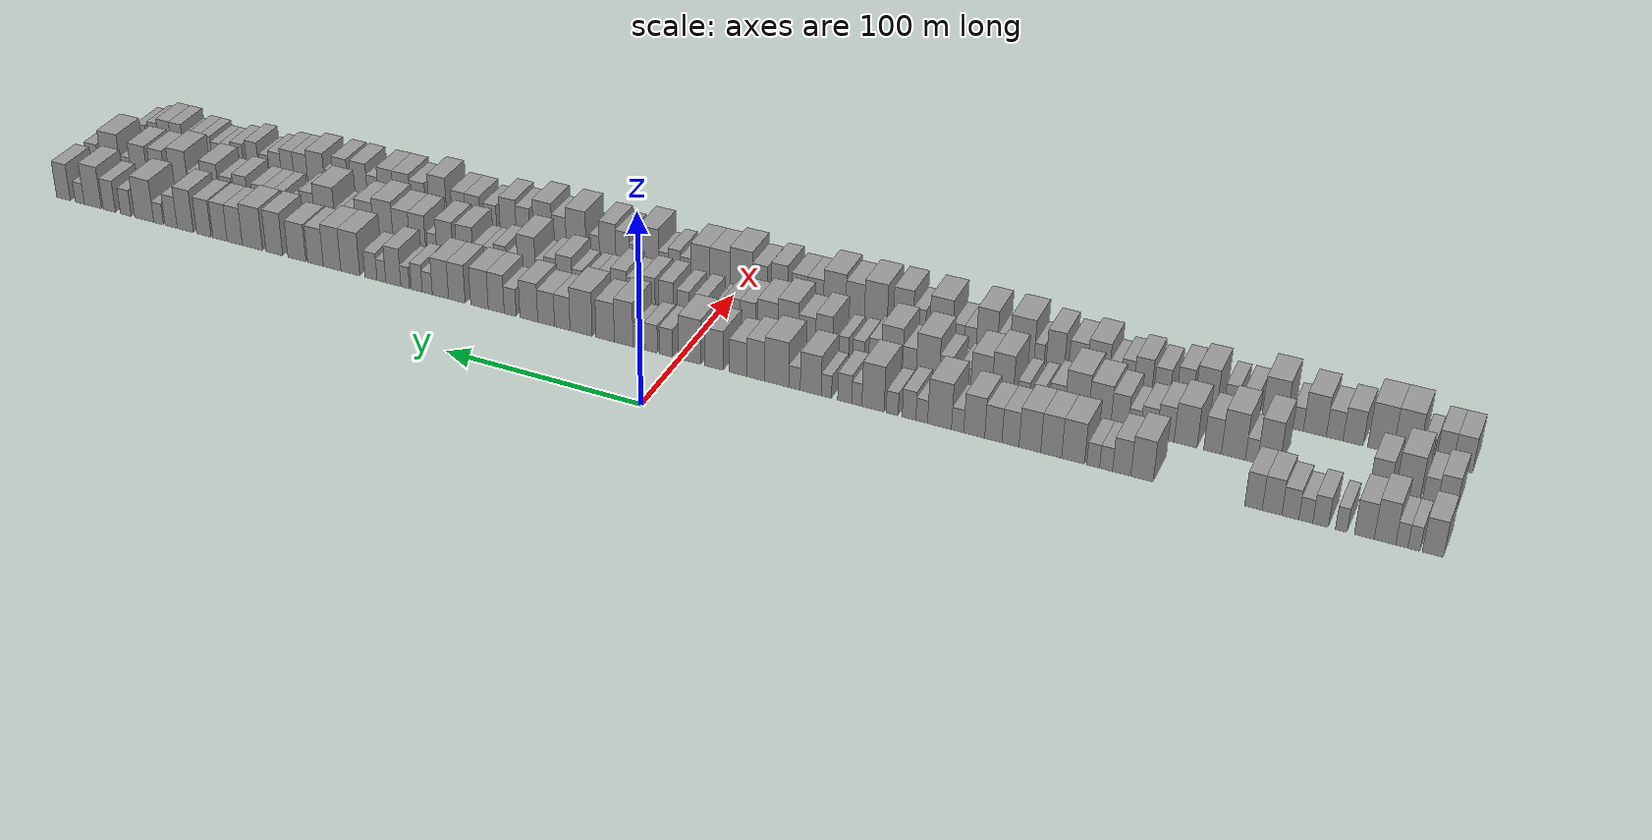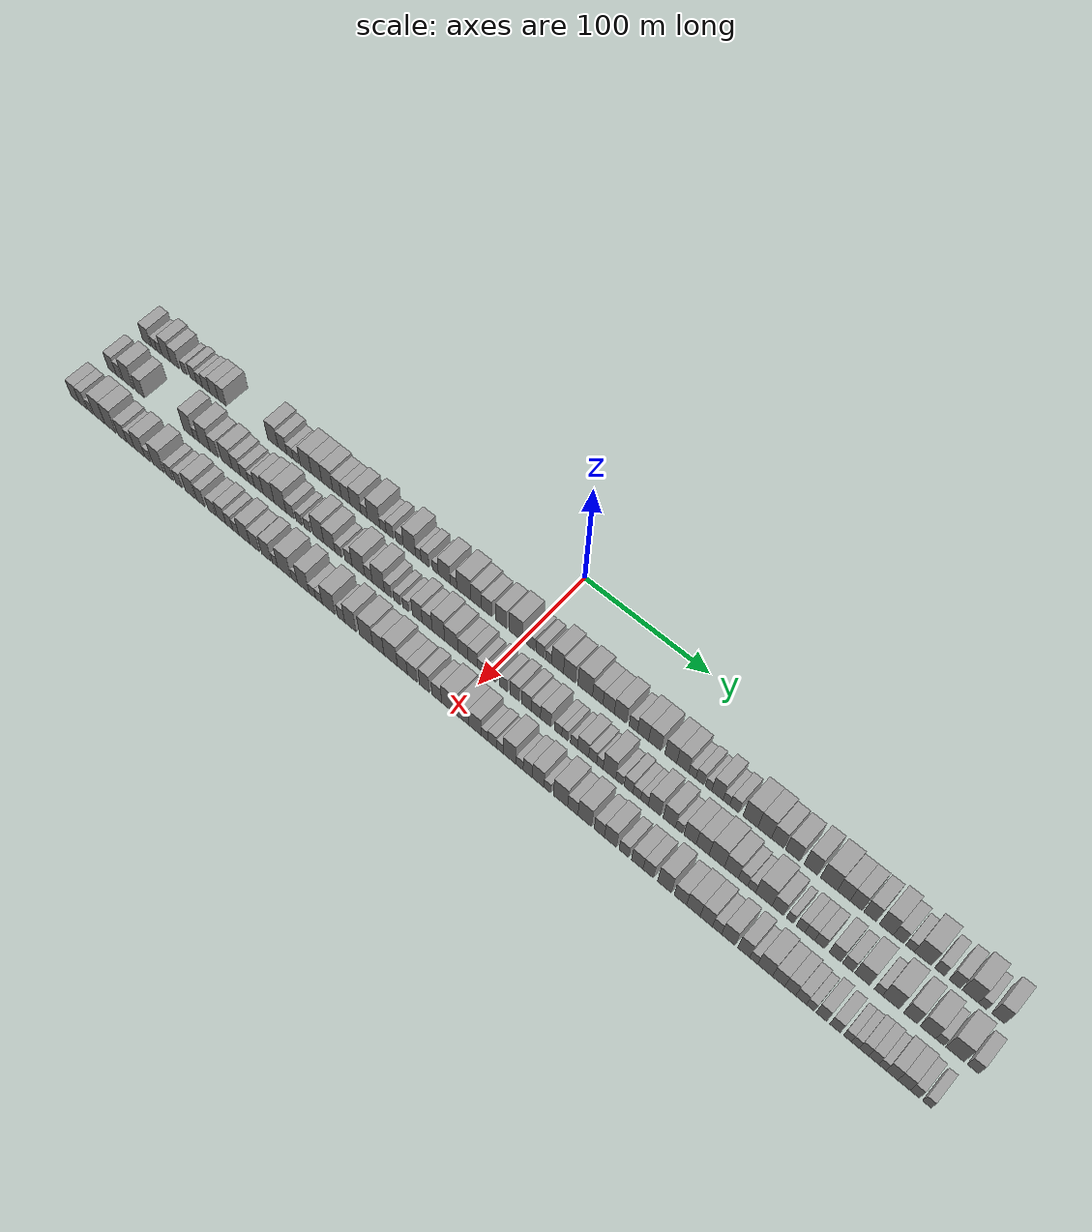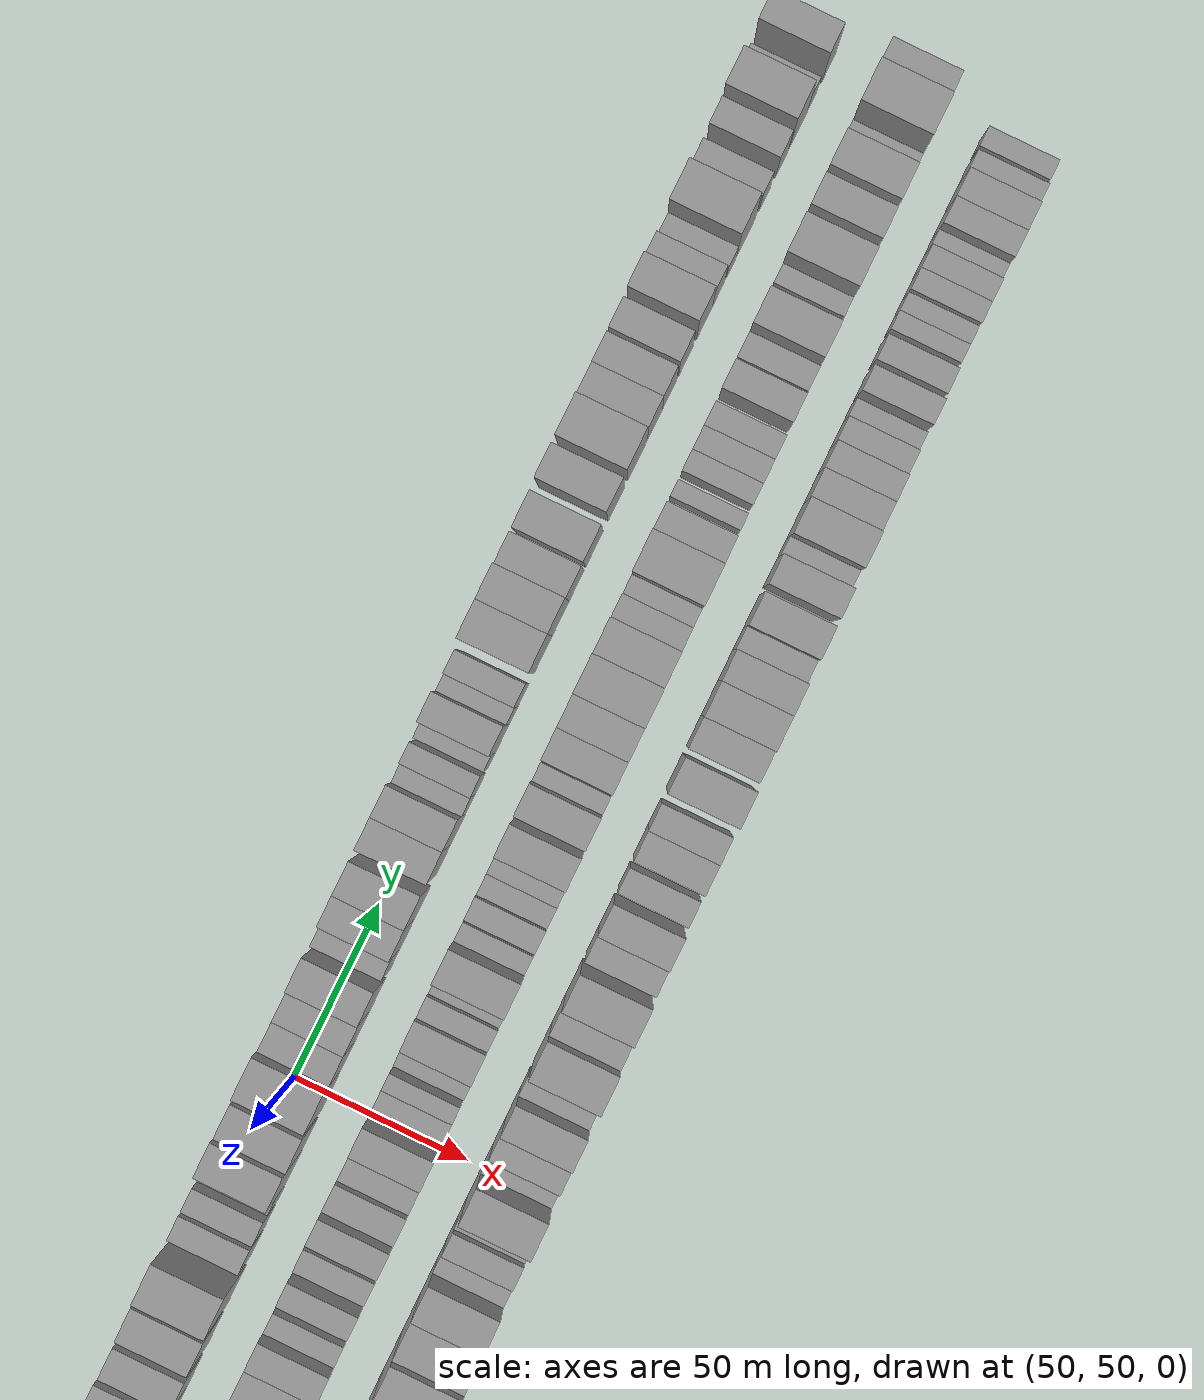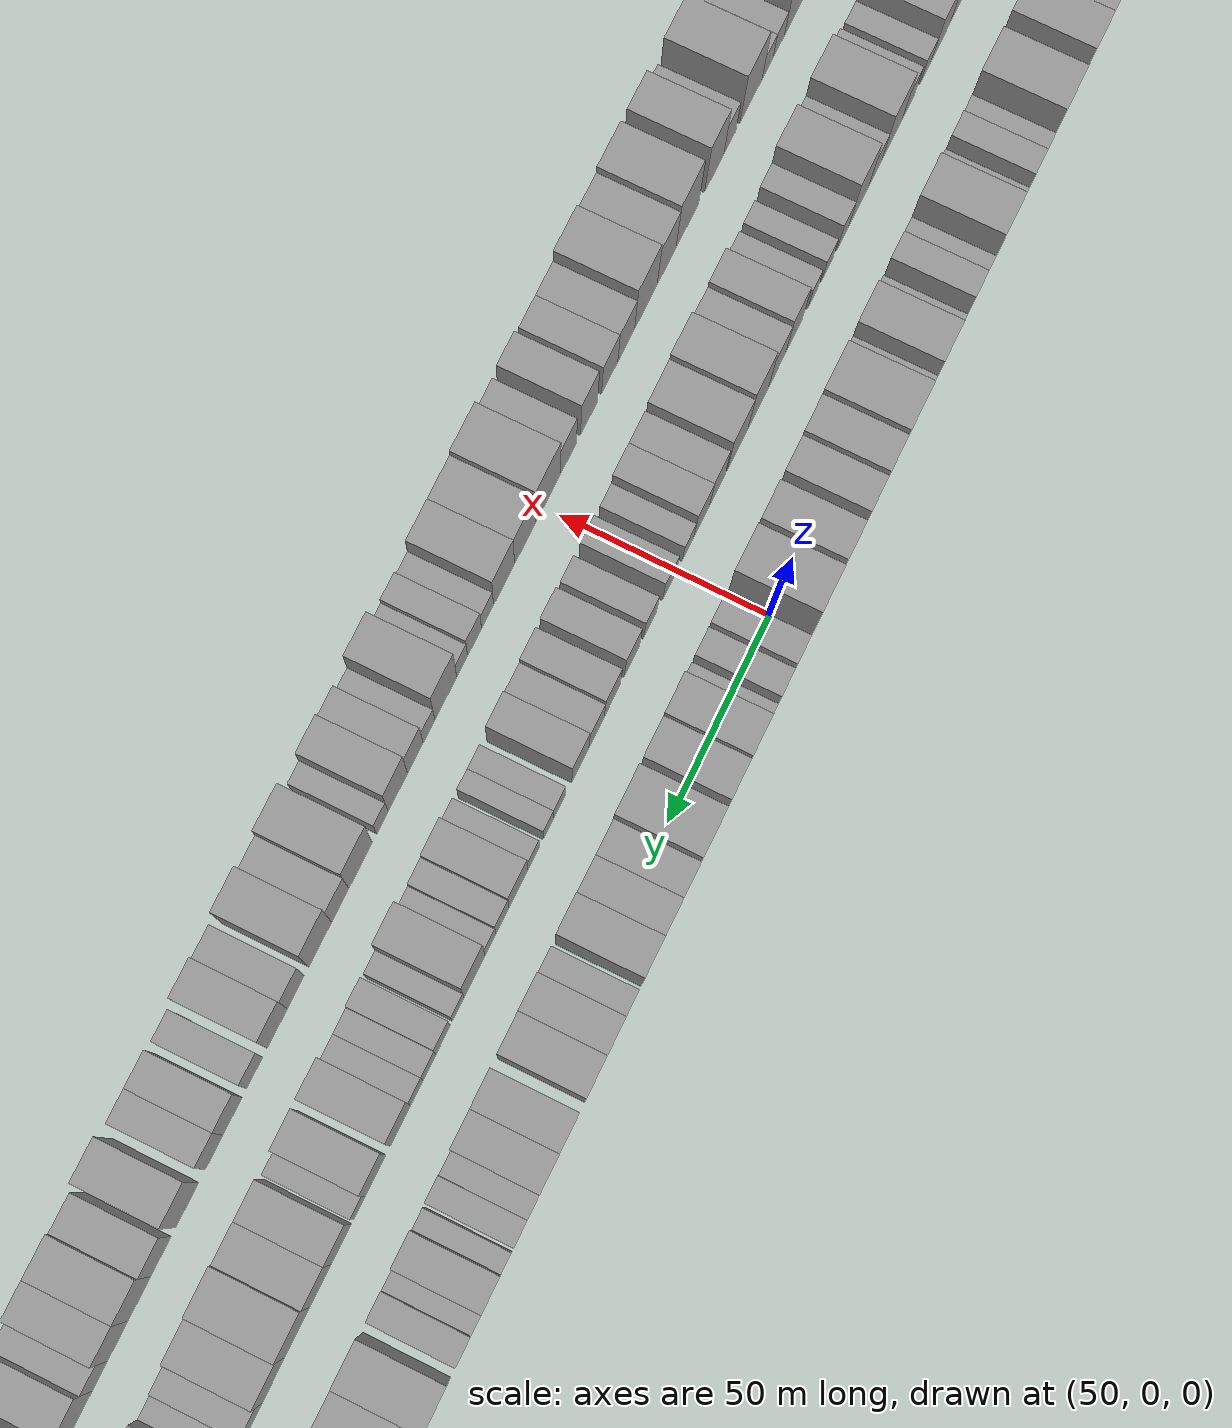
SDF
<sdf version="1.6">
 <world name="default">
  <scene>
   <sky><clouds><speed>12</speed></clouds></sky>
   <ambient>0.4 0.4 0.4 1</ambient>
   <background>0.7 0.7 0.7 1</background>
   <shadows>1</shadows>
  </scene>
  <gravity>0 0 -9.8066</gravity>
  <magnetic_field>6e-06 2.3e-05 -4.2e-05</magnetic_field>
  <physics default="0" name="default_physics" type="ode">
   <ode>
    <solver>
     <type>quick</type>
     <iters>10</iters>
     <sor>1.0</sor>
     <use_dynamic_moi_rescaling>0</use_dynamic_moi_rescaling>
    </solver>
    <constraints>
     <cfm>0</cfm>
     <erp>0.2</erp>
     <contact_max_correcting_vel>100</contact_max_correcting_vel>
     <contact_surface_layer>0.001</contact_surface_layer>
    </constraints>
   </ode>
   <max_step_size>0.004</max_step_size>
   <real_time_factor>1</real_time_factor>
   <real_time_update_rate>250</real_time_update_rate>
  </physics>
  <light name="sun" type="directional">
   <pose>0 0 10 0 0 0</pose>
   <diffuse>0.8 0.8 0.8 1</diffuse>
   <specular>0.2 0.2 0.2 1</specular>
   <attenuation>
    <range>1000</range>
    <constant>0.9</constant>
    <linear>0.01</linear>
    <quadratic>0.001</quadratic>
   </attenuation>
   <direction>-0.5 0.1 -0.9</direction>
  </light>
  <model name="building_1">
   <static>1</static>
   <pose>50.0000 -343.6873 0 0.000000 0.000000 0.000000</pose>
   <link name="link">
    <pose>0 0 9.00 0 0 0</pose>
    <collision name="collision"><geometry><box><size>20.0000 8.6254 18.0000</size></box></geometry></collision>
    <visual name="visual">
     <cast_shadows>0</cast_shadows>
     <geometry><box><size>20.0000 8.6254 18.0000</size></box></geometry>
     <material>
      <script>
       <uri>model://grey_wall/materials/scripts</uri>
       <uri>model://grey_wall/materials/textures</uri>
       <name>vrc/grey_wall</name>
      </script>
     </material>
    </visual>
   </link>
  </model>
  <model name="building_2">
   <static>1</static>
   <pose>50.0000 -335.8789 0 0.000000 0.000000 0.000000</pose>
   <link name="link">
    <pose>0 0 6.00 0 0 0</pose>
    <collision name="collision"><geometry><box><size>20.0000 4.9914 12.0000</size></box></geometry></collision>
    <visual name="visual">
     <cast_shadows>0</cast_shadows>
     <geometry><box><size>20.0000 4.9914 12.0000</size></box></geometry>
     <material>
      <script>
       <uri>model://grey_wall/materials/scripts</uri>
       <uri>model://grey_wall/materials/textures</uri>
       <name>vrc/grey_wall</name>
      </script>
     </material>
    </visual>
   </link>
  </model>
  <model name="building_3">
   <static>1</static>
   <pose>50.0000 -330.8785 0 0.000000 0.000000 0.000000</pose>
   <link name="link">
    <pose>0 0 6.00 0 0 0</pose>
    <collision name="collision"><geometry><box><size>20.0000 5.0094 12.0000</size></box></geometry></collision>
    <visual name="visual">
     <cast_shadows>0</cast_shadows>
     <geometry><box><size>20.0000 5.0094 12.0000</size></box></geometry>
     <material>
      <script>
       <uri>model://grey_wall/materials/scripts</uri>
       <uri>model://grey_wall/materials/textures</uri>
       <name>vrc/grey_wall</name>
      </script>
     </material>
    </visual>
   </link>
  </model>
  <model name="building_4">
   <static>1</static>
   <pose>50.0000 -323.9568 0 0.000000 0.000000 0.000000</pose>
   <link name="link">
    <pose>0 0 10.50 0 0 0</pose>
    <collision name="collision"><geometry><box><size>20.0000 8.8341 21.0000</size></box></geometry></collision>
    <visual name="visual">
     <cast_shadows>0</cast_shadows>
     <geometry><box><size>20.0000 8.8341 21.0000</size></box></geometry>
     <material>
      <script>
       <uri>model://grey_wall/materials/scripts</uri>
       <uri>model://grey_wall/materials/textures</uri>
       <name>vrc/grey_wall</name>
      </script>
     </material>
    </visual>
   </link>
  </model>
  <model name="building_5">
   <static>1</static>
   <pose>50.0000 -315.3958 0 0.000000 0.000000 0.000000</pose>
   <link name="link">
    <pose>0 0 9.00 0 0 0</pose>
    <collision name="collision"><geometry><box><size>20.0000 8.2878 18.0000</size></box></geometry></collision>
    <visual name="visual">
     <cast_shadows>0</cast_shadows>
     <geometry><box><size>20.0000 8.2878 18.0000</size></box></geometry>
     <material>
      <script>
       <uri>model://grey_wall/materials/scripts</uri>
       <uri>model://grey_wall/materials/textures</uri>
       <name>vrc/grey_wall</name>
      </script>
     </material>
    </visual>
   </link>
  </model>
  <model name="building_6">
   <static>1</static>
   <pose>50.0000 -305.8046 0 0.000000 0.000000 0.000000</pose>
   <link name="link">
    <pose>0 0 6.00 0 0 0</pose>
    <collision name="collision"><geometry><box><size>20.0000 4.8945 12.0000</size></box></geometry></collision>
    <visual name="visual">
     <cast_shadows>0</cast_shadows>
     <geometry><box><size>20.0000 4.8945 12.0000</size></box></geometry>
     <material>
      <script>
       <uri>model://grey_wall/materials/scripts</uri>
       <uri>model://grey_wall/materials/textures</uri>
       <name>vrc/grey_wall</name>
      </script>
     </material>
    </visual>
   </link>
  </model>
  <model name="building_7">
   <static>1</static>
   <pose>50.0000 -297.0753 0 0.000000 0.000000 0.000000</pose>
   <link name="link">
    <pose>0 0 7.50 0 0 0</pose>
    <collision name="collision"><geometry><box><size>20.0000 6.5640 15.0000</size></box></geometry></collision>
    <visual name="visual">
     <cast_shadows>0</cast_shadows>
     <geometry><box><size>20.0000 6.5640 15.0000</size></box></geometry>
     <material>
      <script>
       <uri>model://grey_wall/materials/scripts</uri>
       <uri>model://grey_wall/materials/textures</uri>
       <name>vrc/grey_wall</name>
      </script>
     </material>
    </visual>
   </link>
  </model>
  <model name="building_8">
   <static>1</static>
   <pose>50.0000 -290.8603 0 0.000000 0.000000 0.000000</pose>
   <link name="link">
    <pose>0 0 6.00 0 0 0</pose>
    <collision name="collision"><geometry><box><size>20.0000 5.8660 12.0000</size></box></geometry></collision>
    <visual name="visual">
     <cast_shadows>0</cast_shadows>
     <geometry><box><size>20.0000 5.8660 12.0000</size></box></geometry>
     <material>
      <script>
       <uri>model://grey_wall/materials/scripts</uri>
       <uri>model://grey_wall/materials/textures</uri>
       <name>vrc/grey_wall</name>
      </script>
     </material>
    </visual>
   </link>
  </model>
  <model name="building_9">
   <static>1</static>
   <pose>50.0000 -284.3061 0 0.000000 0.000000 0.000000</pose>
   <link name="link">
    <pose>0 0 7.50 0 0 0</pose>
    <collision name="collision"><geometry><box><size>20.0000 7.2424 15.0000</size></box></geometry></collision>
    <visual name="visual">
     <cast_shadows>0</cast_shadows>
     <geometry><box><size>20.0000 7.2424 15.0000</size></box></geometry>
     <material>
      <script>
       <uri>model://grey_wall/materials/scripts</uri>
       <uri>model://grey_wall/materials/textures</uri>
       <name>vrc/grey_wall</name>
      </script>
     </material>
    </visual>
   </link>
  </model>
  <model name="building_10">
   <static>1</static>
   <pose>50.0000 -276.5179 0 0.000000 0.000000 0.000000</pose>
   <link name="link">
    <pose>0 0 9.00 0 0 0</pose>
    <collision name="collision"><geometry><box><size>20.0000 8.3341 18.0000</size></box></geometry></collision>
    <visual name="visual">
     <cast_shadows>0</cast_shadows>
     <geometry><box><size>20.0000 8.3341 18.0000</size></box></geometry>
     <material>
      <script>
       <uri>model://grey_wall/materials/scripts</uri>
       <uri>model://grey_wall/materials/textures</uri>
       <name>vrc/grey_wall</name>
      </script>
     </material>
    </visual>
   </link>
  </model>
  <model name="building_11">
   <static>1</static>
   <pose>50.0000 -268.5844 0 0.000000 0.000000 0.000000</pose>
   <link name="link">
    <pose>0 0 9.00 0 0 0</pose>
    <collision name="collision"><geometry><box><size>20.0000 7.5328 18.0000</size></box></geometry></collision>
    <visual name="visual">
     <cast_shadows>0</cast_shadows>
     <geometry><box><size>20.0000 7.5328 18.0000</size></box></geometry>
     <material>
      <script>
       <uri>model://grey_wall/materials/scripts</uri>
       <uri>model://grey_wall/materials/textures</uri>
       <name>vrc/grey_wall</name>
      </script>
     </material>
    </visual>
   </link>
  </model>
  <model name="building_12">
   <static>1</static>
   <pose>50.0000 -219.9695 0 0.000000 0.000000 0.000000</pose>
   <link name="link">
    <pose>0 0 10.50 0 0 0</pose>
    <collision name="collision"><geometry><box><size>20.0000 9.8990 21.0000</size></box></geometry></collision>
    <visual name="visual">
     <cast_shadows>0</cast_shadows>
     <geometry><box><size>20.0000 9.8990 21.0000</size></box></geometry>
     <material>
      <script>
       <uri>model://grey_wall/materials/scripts</uri>
       <uri>model://grey_wall/materials/textures</uri>
       <name>vrc/grey_wall</name>
      </script>
     </material>
    </visual>
   </link>
  </model>
  <model name="building_13">
   <static>1</static>
   <pose>50.0000 -210.9266 0 0.000000 0.000000 0.000000</pose>
   <link name="link">
    <pose>0 0 9.00 0 0 0</pose>
    <collision name="collision"><geometry><box><size>20.0000 8.1867 18.0000</size></box></geometry></collision>
    <visual name="visual">
     <cast_shadows>0</cast_shadows>
     <geometry><box><size>20.0000 8.1867 18.0000</size></box></geometry>
     <material>
      <script>
       <uri>model://grey_wall/materials/scripts</uri>
       <uri>model://grey_wall/materials/textures</uri>
       <name>vrc/grey_wall</name>
      </script>
     </material>
    </visual>
   </link>
  </model>
  <model name="building_14">
   <static>1</static>
   <pose>50.0000 -203.9265 0 0.000000 0.000000 0.000000</pose>
   <link name="link">
    <pose>0 0 6.00 0 0 0</pose>
    <collision name="collision"><geometry><box><size>20.0000 5.8134 12.0000</size></box></geometry></collision>
    <visual name="visual">
     <cast_shadows>0</cast_shadows>
     <geometry><box><size>20.0000 5.8134 12.0000</size></box></geometry>
     <material>
      <script>
       <uri>model://grey_wall/materials/scripts</uri>
       <uri>model://grey_wall/materials/textures</uri>
       <name>vrc/grey_wall</name>
      </script>
     </material>
    </visual>
   </link>
  </model>
  <model name="building_15">
   <static>1</static>
   <pose>50.0000 -198.1525 0 0.000000 0.000000 0.000000</pose>
   <link name="link">
    <pose>0 0 6.00 0 0 0</pose>
    <collision name="collision"><geometry><box><size>20.0000 5.7346 12.0000</size></box></geometry></collision>
    <visual name="visual">
     <cast_shadows>0</cast_shadows>
     <geometry><box><size>20.0000 5.7346 12.0000</size></box></geometry>
     <material>
      <script>
       <uri>model://grey_wall/materials/scripts</uri>
       <uri>model://grey_wall/materials/textures</uri>
       <name>vrc/grey_wall</name>
      </script>
     </material>
    </visual>
   </link>
  </model>
  <model name="building_16">
   <static>1</static>
   <pose>50.0000 -189.0835 0 0.000000 0.000000 0.000000</pose>
   <link name="link">
    <pose>0 0 10.50 0 0 0</pose>
    <collision name="collision"><geometry><box><size>20.0000 10.4035 21.0000</size></box></geometry></collision>
    <visual name="visual">
     <cast_shadows>0</cast_shadows>
     <geometry><box><size>20.0000 10.4035 21.0000</size></box></geometry>
     <material>
      <script>
       <uri>model://grey_wall/materials/scripts</uri>
       <uri>model://grey_wall/materials/textures</uri>
       <name>vrc/grey_wall</name>
      </script>
     </material>
    </visual>
   </link>
  </model>
  <model name="building_17">
   <static>1</static>
   <pose>50.0000 -179.0942 0 0.000000 0.000000 0.000000</pose>
   <link name="link">
    <pose>0 0 10.50 0 0 0</pose>
    <collision name="collision"><geometry><box><size>20.0000 9.5750 21.0000</size></box></geometry></collision>
    <visual name="visual">
     <cast_shadows>0</cast_shadows>
     <geometry><box><size>20.0000 9.5750 21.0000</size></box></geometry>
     <material>
      <script>
       <uri>model://grey_wall/materials/scripts</uri>
       <uri>model://grey_wall/materials/textures</uri>
       <name>vrc/grey_wall</name>
      </script>
     </material>
    </visual>
   </link>
  </model>
  <model name="building_18">
   <static>1</static>
   <pose>50.0000 -169.3435 0 0.000000 0.000000 0.000000</pose>
   <link name="link">
    <pose>0 0 10.50 0 0 0</pose>
    <collision name="collision"><geometry><box><size>20.0000 9.9265 21.0000</size></box></geometry></collision>
    <visual name="visual">
     <cast_shadows>0</cast_shadows>
     <geometry><box><size>20.0000 9.9265 21.0000</size></box></geometry>
     <material>
      <script>
       <uri>model://grey_wall/materials/scripts</uri>
       <uri>model://grey_wall/materials/textures</uri>
       <name>vrc/grey_wall</name>
      </script>
     </material>
    </visual>
   </link>
  </model>
  <model name="building_19">
   <static>1</static>
   <pose>50.0000 -160.4506 0 0.000000 0.000000 0.000000</pose>
   <link name="link">
    <pose>0 0 9.00 0 0 0</pose>
    <collision name="collision"><geometry><box><size>20.0000 7.8593 18.0000</size></box></geometry></collision>
    <visual name="visual">
     <cast_shadows>0</cast_shadows>
     <geometry><box><size>20.0000 7.8593 18.0000</size></box></geometry>
     <material>
      <script>
       <uri>model://grey_wall/materials/scripts</uri>
       <uri>model://grey_wall/materials/textures</uri>
       <name>vrc/grey_wall</name>
      </script>
     </material>
    </visual>
   </link>
  </model>
  <model name="building_20">
   <static>1</static>
   <pose>50.0000 -152.5417 0 0.000000 0.000000 0.000000</pose>
   <link name="link">
    <pose>0 0 9.00 0 0 0</pose>
    <collision name="collision"><geometry><box><size>20.0000 7.9585 18.0000</size></box></geometry></collision>
    <visual name="visual">
     <cast_shadows>0</cast_shadows>
     <geometry><box><size>20.0000 7.9585 18.0000</size></box></geometry>
     <material>
      <script>
       <uri>model://grey_wall/materials/scripts</uri>
       <uri>model://grey_wall/materials/textures</uri>
       <name>vrc/grey_wall</name>
      </script>
     </material>
    </visual>
   </link>
  </model>
  <model name="building_21">
   <static>1</static>
   <pose>50.0000 -143.6699 0 0.000000 0.000000 0.000000</pose>
   <link name="link">
    <pose>0 0 10.50 0 0 0</pose>
    <collision name="collision"><geometry><box><size>20.0000 9.7850 21.0000</size></box></geometry></collision>
    <visual name="visual">
     <cast_shadows>0</cast_shadows>
     <geometry><box><size>20.0000 9.7850 21.0000</size></box></geometry>
     <material>
      <script>
       <uri>model://grey_wall/materials/scripts</uri>
       <uri>model://grey_wall/materials/textures</uri>
       <name>vrc/grey_wall</name>
      </script>
     </material>
    </visual>
   </link>
  </model>
  <model name="building_22">
   <static>1</static>
   <pose>50.0000 -135.9122 0 0.000000 0.000000 0.000000</pose>
   <link name="link">
    <pose>0 0 6.00 0 0 0</pose>
    <collision name="collision"><geometry><box><size>20.0000 5.7304 12.0000</size></box></geometry></collision>
    <visual name="visual">
     <cast_shadows>0</cast_shadows>
     <geometry><box><size>20.0000 5.7304 12.0000</size></box></geometry>
     <material>
      <script>
       <uri>model://grey_wall/materials/scripts</uri>
       <uri>model://grey_wall/materials/textures</uri>
       <name>vrc/grey_wall</name>
      </script>
     </material>
    </visual>
   </link>
  </model>
  <model name="building_23">
   <static>1</static>
   <pose>50.0000 -127.4148 0 0.000000 0.000000 0.000000</pose>
   <link name="link">
    <pose>0 0 12.00 0 0 0</pose>
    <collision name="collision"><geometry><box><size>20.0000 11.2644 24.0000</size></box></geometry></collision>
    <visual name="visual">
     <cast_shadows>0</cast_shadows>
     <geometry><box><size>20.0000 11.2644 24.0000</size></box></geometry>
     <material>
      <script>
       <uri>model://grey_wall/materials/scripts</uri>
       <uri>model://grey_wall/materials/textures</uri>
       <name>vrc/grey_wall</name>
      </script>
     </material>
    </visual>
   </link>
  </model>
  <model name="building_24">
   <static>1</static>
   <pose>50.0000 -118.9995 0 0.000000 0.000000 0.000000</pose>
   <link name="link">
    <pose>0 0 6.00 0 0 0</pose>
    <collision name="collision"><geometry><box><size>20.0000 5.5662 12.0000</size></box></geometry></collision>
    <visual name="visual">
     <cast_shadows>0</cast_shadows>
     <geometry><box><size>20.0000 5.5662 12.0000</size></box></geometry>
     <material>
      <script>
       <uri>model://grey_wall/materials/scripts</uri>
       <uri>model://grey_wall/materials/textures</uri>
       <name>vrc/grey_wall</name>
      </script>
     </material>
    </visual>
   </link>
  </model>
  <model name="building_25">
   <static>1</static>
   <pose>50.0000 -112.9976 0 0.000000 0.000000 0.000000</pose>
   <link name="link">
    <pose>0 0 7.50 0 0 0</pose>
    <collision name="collision"><geometry><box><size>20.0000 6.4377 15.0000</size></box></geometry></collision>
    <visual name="visual">
     <cast_shadows>0</cast_shadows>
     <geometry><box><size>20.0000 6.4377 15.0000</size></box></geometry>
     <material>
      <script>
       <uri>model://grey_wall/materials/scripts</uri>
       <uri>model://grey_wall/materials/textures</uri>
       <name>vrc/grey_wall</name>
      </script>
     </material>
    </visual>
   </link>
  </model>
  <model name="building_26">
   <static>1</static>
   <pose>50.0000 -104.9338 0 0.000000 0.000000 0.000000</pose>
   <link name="link">
    <pose>0 0 6.00 0 0 0</pose>
    <collision name="collision"><geometry><box><size>20.0000 5.6898 12.0000</size></box></geometry></collision>
    <visual name="visual">
     <cast_shadows>0</cast_shadows>
     <geometry><box><size>20.0000 5.6898 12.0000</size></box></geometry>
     <material>
      <script>
       <uri>model://grey_wall/materials/scripts</uri>
       <uri>model://grey_wall/materials/textures</uri>
       <name>vrc/grey_wall</name>
      </script>
     </material>
    </visual>
   </link>
  </model>
  <model name="building_27">
   <static>1</static>
   <pose>50.0000 -95.7487 0 0.000000 0.000000 0.000000</pose>
   <link name="link">
    <pose>0 0 12.00 0 0 0</pose>
    <collision name="collision"><geometry><box><size>20.0000 10.6804 24.0000</size></box></geometry></collision>
    <visual name="visual">
     <cast_shadows>0</cast_shadows>
     <geometry><box><size>20.0000 10.6804 24.0000</size></box></geometry>
     <material>
      <script>
       <uri>model://grey_wall/materials/scripts</uri>
       <uri>model://grey_wall/materials/textures</uri>
       <name>vrc/grey_wall</name>
      </script>
     </material>
    </visual>
   </link>
  </model>
  <model name="building_28">
   <static>1</static>
   <pose>50.0000 -87.9638 0 0.000000 0.000000 0.000000</pose>
   <link name="link">
    <pose>0 0 6.00 0 0 0</pose>
    <collision name="collision"><geometry><box><size>20.0000 4.8894 12.0000</size></box></geometry></collision>
    <visual name="visual">
     <cast_shadows>0</cast_shadows>
     <geometry><box><size>20.0000 4.8894 12.0000</size></box></geometry>
     <material>
      <script>
       <uri>model://grey_wall/materials/scripts</uri>
       <uri>model://grey_wall/materials/textures</uri>
       <name>vrc/grey_wall</name>
      </script>
     </material>
    </visual>
   </link>
  </model>
  <model name="building_29">
   <static>1</static>
   <pose>50.0000 -82.1213 0 0.000000 0.000000 0.000000</pose>
   <link name="link">
    <pose>0 0 7.50 0 0 0</pose>
    <collision name="collision"><geometry><box><size>20.0000 6.7956 15.0000</size></box></geometry></collision>
    <visual name="visual">
     <cast_shadows>0</cast_shadows>
     <geometry><box><size>20.0000 6.7956 15.0000</size></box></geometry>
     <material>
      <script>
       <uri>model://grey_wall/materials/scripts</uri>
       <uri>model://grey_wall/materials/textures</uri>
       <name>vrc/grey_wall</name>
      </script>
     </material>
    </visual>
   </link>
  </model>
  <model name="building_30">
   <static>1</static>
   <pose>50.0000 -73.1943 0 0.000000 0.000000 0.000000</pose>
   <link name="link">
    <pose>0 0 6.00 0 0 0</pose>
    <collision name="collision"><geometry><box><size>20.0000 5.0585 12.0000</size></box></geometry></collision>
    <visual name="visual">
     <cast_shadows>0</cast_shadows>
     <geometry><box><size>20.0000 5.0585 12.0000</size></box></geometry>
     <material>
      <script>
       <uri>model://grey_wall/materials/scripts</uri>
       <uri>model://grey_wall/materials/textures</uri>
       <name>vrc/grey_wall</name>
      </script>
     </material>
    </visual>
   </link>
  </model>
  <model name="building_31">
   <static>1</static>
   <pose>50.0000 -65.5477 0 0.000000 0.000000 0.000000</pose>
   <link name="link">
    <pose>0 0 10.50 0 0 0</pose>
    <collision name="collision"><geometry><box><size>20.0000 10.2346 21.0000</size></box></geometry></collision>
    <visual name="visual">
     <cast_shadows>0</cast_shadows>
     <geometry><box><size>20.0000 10.2346 21.0000</size></box></geometry>
     <material>
      <script>
       <uri>model://grey_wall/materials/scripts</uri>
       <uri>model://grey_wall/materials/textures</uri>
       <name>vrc/grey_wall</name>
      </script>
     </material>
    </visual>
   </link>
  </model>
  <model name="building_32">
   <static>1</static>
   <pose>50.0000 -57.5877 0 0.000000 0.000000 0.000000</pose>
   <link name="link">
    <pose>0 0 6.00 0 0 0</pose>
    <collision name="collision"><geometry><box><size>20.0000 5.6855 12.0000</size></box></geometry></collision>
    <visual name="visual">
     <cast_shadows>0</cast_shadows>
     <geometry><box><size>20.0000 5.6855 12.0000</size></box></geometry>
     <material>
      <script>
       <uri>model://grey_wall/materials/scripts</uri>
       <uri>model://grey_wall/materials/textures</uri>
       <name>vrc/grey_wall</name>
      </script>
     </material>
    </visual>
   </link>
  </model>
  <model name="building_33">
   <static>1</static>
   <pose>50.0000 -48.7730 0 0.000000 0.000000 0.000000</pose>
   <link name="link">
    <pose>0 0 12.00 0 0 0</pose>
    <collision name="collision"><geometry><box><size>20.0000 11.9438 24.0000</size></box></geometry></collision>
    <visual name="visual">
     <cast_shadows>0</cast_shadows>
     <geometry><box><size>20.0000 11.9438 24.0000</size></box></geometry>
     <material>
      <script>
       <uri>model://grey_wall/materials/scripts</uri>
       <uri>model://grey_wall/materials/textures</uri>
       <name>vrc/grey_wall</name>
      </script>
     </material>
    </visual>
   </link>
  </model>
  <model name="building_34">
   <static>1</static>
   <pose>50.0000 -38.3306 0 0.000000 0.000000 0.000000</pose>
   <link name="link">
    <pose>0 0 10.50 0 0 0</pose>
    <collision name="collision"><geometry><box><size>20.0000 8.9411 21.0000</size></box></geometry></collision>
    <visual name="visual">
     <cast_shadows>0</cast_shadows>
     <geometry><box><size>20.0000 8.9411 21.0000</size></box></geometry>
     <material>
      <script>
       <uri>model://grey_wall/materials/scripts</uri>
       <uri>model://grey_wall/materials/textures</uri>
       <name>vrc/grey_wall</name>
      </script>
     </material>
    </visual>
   </link>
  </model>
  <model name="building_35">
   <static>1</static>
   <pose>50.0000 -29.5193 0 0.000000 0.000000 0.000000</pose>
   <link name="link">
    <pose>0 0 9.00 0 0 0</pose>
    <collision name="collision"><geometry><box><size>20.0000 8.6813 18.0000</size></box></geometry></collision>
    <visual name="visual">
     <cast_shadows>0</cast_shadows>
     <geometry><box><size>20.0000 8.6813 18.0000</size></box></geometry>
     <material>
      <script>
       <uri>model://grey_wall/materials/scripts</uri>
       <uri>model://grey_wall/materials/textures</uri>
       <name>vrc/grey_wall</name>
      </script>
     </material>
    </visual>
   </link>
  </model>
  <model name="building_36">
   <static>1</static>
   <pose>50.0000 -17.4977 0 0.000000 0.000000 0.000000</pose>
   <link name="link">
    <pose>0 0 10.50 0 0 0</pose>
    <collision name="collision"><geometry><box><size>20.0000 9.3620 21.0000</size></box></geometry></collision>
    <visual name="visual">
     <cast_shadows>0</cast_shadows>
     <geometry><box><size>20.0000 9.3620 21.0000</size></box></geometry>
     <material>
      <script>
       <uri>model://grey_wall/materials/scripts</uri>
       <uri>model://grey_wall/materials/textures</uri>
       <name>vrc/grey_wall</name>
      </script>
     </material>
    </visual>
   </link>
  </model>
  <model name="building_37">
   <static>1</static>
   <pose>50.0000 -5.1699 0 0.000000 0.000000 0.000000</pose>
   <link name="link">
    <pose>0 0 12.00 0 0 0</pose>
    <collision name="collision"><geometry><box><size>20.0000 11.2936 24.0000</size></box></geometry></collision>
    <visual name="visual">
     <cast_shadows>0</cast_shadows>
     <geometry><box><size>20.0000 11.2936 24.0000</size></box></geometry>
     <material>
      <script>
       <uri>model://grey_wall/materials/scripts</uri>
       <uri>model://grey_wall/materials/textures</uri>
       <name>vrc/grey_wall</name>
      </script>
     </material>
    </visual>
   </link>
  </model>
  <model name="building_38">
   <static>1</static>
   <pose>50.0000 6.9233 0 0.000000 0.000000 0.000000</pose>
   <link name="link">
    <pose>0 0 7.50 0 0 0</pose>
    <collision name="collision"><geometry><box><size>20.0000 6.8927 15.0000</size></box></geometry></collision>
    <visual name="visual">
     <cast_shadows>0</cast_shadows>
     <geometry><box><size>20.0000 6.8927 15.0000</size></box></geometry>
     <material>
      <script>
       <uri>model://grey_wall/materials/scripts</uri>
       <uri>model://grey_wall/materials/textures</uri>
       <name>vrc/grey_wall</name>
      </script>
     </material>
    </visual>
   </link>
  </model>
  <model name="building_39">
   <static>1</static>
   <pose>50.0000 14.7206 0 0.000000 0.000000 0.000000</pose>
   <link name="link">
    <pose>0 0 7.50 0 0 0</pose>
    <collision name="collision"><geometry><box><size>20.0000 6.7020 15.0000</size></box></geometry></collision>
    <visual name="visual">
     <cast_shadows>0</cast_shadows>
     <geometry><box><size>20.0000 6.7020 15.0000</size></box></geometry>
     <material>
      <script>
       <uri>model://grey_wall/materials/scripts</uri>
       <uri>model://grey_wall/materials/textures</uri>
       <name>vrc/grey_wall</name>
      </script>
     </material>
    </visual>
   </link>
  </model>
  <model name="building_40">
   <static>1</static>
   <pose>50.0000 21.5053 0 0.000000 0.000000 0.000000</pose>
   <link name="link">
    <pose>0 0 6.00 0 0 0</pose>
    <collision name="collision"><geometry><box><size>20.0000 4.8674 12.0000</size></box></geometry></collision>
    <visual name="visual">
     <cast_shadows>0</cast_shadows>
     <geometry><box><size>20.0000 4.8674 12.0000</size></box></geometry>
     <material>
      <script>
       <uri>model://grey_wall/materials/scripts</uri>
       <uri>model://grey_wall/materials/textures</uri>
       <name>vrc/grey_wall</name>
      </script>
     </material>
    </visual>
   </link>
  </model>
  <model name="building_41">
   <static>1</static>
   <pose>50.0000 28.7867 0 0.000000 0.000000 0.000000</pose>
   <link name="link">
    <pose>0 0 12.00 0 0 0</pose>
    <collision name="collision"><geometry><box><size>20.0000 9.6955 24.0000</size></box></geometry></collision>
    <visual name="visual">
     <cast_shadows>0</cast_shadows>
     <geometry><box><size>20.0000 9.6955 24.0000</size></box></geometry>
     <material>
      <script>
       <uri>model://grey_wall/materials/scripts</uri>
       <uri>model://grey_wall/materials/textures</uri>
       <name>vrc/grey_wall</name>
      </script>
     </material>
    </visual>
   </link>
  </model>
  <model name="building_42">
   <static>1</static>
   <pose>50.0000 38.4106 0 0.000000 0.000000 0.000000</pose>
   <link name="link">
    <pose>0 0 10.50 0 0 0</pose>
    <collision name="collision"><geometry><box><size>20.0000 9.5522 21.0000</size></box></geometry></collision>
    <visual name="visual">
     <cast_shadows>0</cast_shadows>
     <geometry><box><size>20.0000 9.5522 21.0000</size></box></geometry>
     <material>
      <script>
       <uri>model://grey_wall/materials/scripts</uri>
       <uri>model://grey_wall/materials/textures</uri>
       <name>vrc/grey_wall</name>
      </script>
     </material>
    </visual>
   </link>
  </model>
  <model name="building_43">
   <static>1</static>
   <pose>50.0000 51.0398 0 0.000000 0.000000 0.000000</pose>
   <link name="link">
    <pose>0 0 12.00 0 0 0</pose>
    <collision name="collision"><geometry><box><size>20.0000 11.7063 24.0000</size></box></geometry></collision>
    <visual name="visual">
     <cast_shadows>0</cast_shadows>
     <geometry><box><size>20.0000 11.7063 24.0000</size></box></geometry>
     <material>
      <script>
       <uri>model://grey_wall/materials/scripts</uri>
       <uri>model://grey_wall/materials/textures</uri>
       <name>vrc/grey_wall</name>
      </script>
     </material>
    </visual>
   </link>
  </model>
  <model name="building_44">
   <static>1</static>
   <pose>50.0000 61.0070 0 0.000000 0.000000 0.000000</pose>
   <link name="link">
    <pose>0 0 9.00 0 0 0</pose>
    <collision name="collision"><geometry><box><size>20.0000 8.2280 18.0000</size></box></geometry></collision>
    <visual name="visual">
     <cast_shadows>0</cast_shadows>
     <geometry><box><size>20.0000 8.2280 18.0000</size></box></geometry>
     <material>
      <script>
       <uri>model://grey_wall/materials/scripts</uri>
       <uri>model://grey_wall/materials/textures</uri>
       <name>vrc/grey_wall</name>
      </script>
     </material>
    </visual>
   </link>
  </model>
  <model name="building_45">
   <static>1</static>
   <pose>50.0000 69.5817 0 0.000000 0.000000 0.000000</pose>
   <link name="link">
    <pose>0 0 9.00 0 0 0</pose>
    <collision name="collision"><geometry><box><size>20.0000 8.9216 18.0000</size></box></geometry></collision>
    <visual name="visual">
     <cast_shadows>0</cast_shadows>
     <geometry><box><size>20.0000 8.9216 18.0000</size></box></geometry>
     <material>
      <script>
       <uri>model://grey_wall/materials/scripts</uri>
       <uri>model://grey_wall/materials/textures</uri>
       <name>vrc/grey_wall</name>
      </script>
     </material>
    </visual>
   </link>
  </model>
  <model name="building_46">
   <static>1</static>
   <pose>50.0000 78.8155 0 0.000000 0.000000 0.000000</pose>
   <link name="link">
    <pose>0 0 10.50 0 0 0</pose>
    <collision name="collision"><geometry><box><size>20.0000 9.5459 21.0000</size></box></geometry></collision>
    <visual name="visual">
     <cast_shadows>0</cast_shadows>
     <geometry><box><size>20.0000 9.5459 21.0000</size></box></geometry>
     <material>
      <script>
       <uri>model://grey_wall/materials/scripts</uri>
       <uri>model://grey_wall/materials/textures</uri>
       <name>vrc/grey_wall</name>
      </script>
     </material>
    </visual>
   </link>
  </model>
  <model name="building_47">
   <static>1</static>
   <pose>50.0000 88.8170 0 0.000000 0.000000 0.000000</pose>
   <link name="link">
    <pose>0 0 7.50 0 0 0</pose>
    <collision name="collision"><geometry><box><size>20.0000 6.4572 15.0000</size></box></geometry></collision>
    <visual name="visual">
     <cast_shadows>0</cast_shadows>
     <geometry><box><size>20.0000 6.4572 15.0000</size></box></geometry>
     <material>
      <script>
       <uri>model://grey_wall/materials/scripts</uri>
       <uri>model://grey_wall/materials/textures</uri>
       <name>vrc/grey_wall</name>
      </script>
     </material>
    </visual>
   </link>
  </model>
  <model name="building_48">
   <static>1</static>
   <pose>50.0000 96.3741 0 0.000000 0.000000 0.000000</pose>
   <link name="link">
    <pose>0 0 10.50 0 0 0</pose>
    <collision name="collision"><geometry><box><size>20.0000 8.6570 21.0000</size></box></geometry></collision>
    <visual name="visual">
     <cast_shadows>0</cast_shadows>
     <geometry><box><size>20.0000 8.6570 21.0000</size></box></geometry>
     <material>
      <script>
       <uri>model://grey_wall/materials/scripts</uri>
       <uri>model://grey_wall/materials/textures</uri>
       <name>vrc/grey_wall</name>
      </script>
     </material>
    </visual>
   </link>
  </model>
  <model name="building_49">
   <static>1</static>
   <pose>50.0000 105.4882 0 0.000000 0.000000 0.000000</pose>
   <link name="link">
    <pose>0 0 10.50 0 0 0</pose>
    <collision name="collision"><geometry><box><size>20.0000 9.5713 21.0000</size></box></geometry></collision>
    <visual name="visual">
     <cast_shadows>0</cast_shadows>
     <geometry><box><size>20.0000 9.5713 21.0000</size></box></geometry>
     <material>
      <script>
       <uri>model://grey_wall/materials/scripts</uri>
       <uri>model://grey_wall/materials/textures</uri>
       <name>vrc/grey_wall</name>
      </script>
     </material>
    </visual>
   </link>
  </model>
  <model name="building_50">
   <static>1</static>
   <pose>50.0000 117.8128 0 0.000000 0.000000 0.000000</pose>
   <link name="link">
    <pose>0 0 10.50 0 0 0</pose>
    <collision name="collision"><geometry><box><size>20.0000 9.0778 21.0000</size></box></geometry></collision>
    <visual name="visual">
     <cast_shadows>0</cast_shadows>
     <geometry><box><size>20.0000 9.0778 21.0000</size></box></geometry>
     <material>
      <script>
       <uri>model://grey_wall/materials/scripts</uri>
       <uri>model://grey_wall/materials/textures</uri>
       <name>vrc/grey_wall</name>
      </script>
     </material>
    </visual>
   </link>
  </model>
  <model name="building_51">
   <static>1</static>
   <pose>50.0000 126.8346 0 0.000000 0.000000 0.000000</pose>
   <link name="link">
    <pose>0 0 10.50 0 0 0</pose>
    <collision name="collision"><geometry><box><size>20.0000 8.9659 21.0000</size></box></geometry></collision>
    <visual name="visual">
     <cast_shadows>0</cast_shadows>
     <geometry><box><size>20.0000 8.9659 21.0000</size></box></geometry>
     <material>
      <script>
       <uri>model://grey_wall/materials/scripts</uri>
       <uri>model://grey_wall/materials/textures</uri>
       <name>vrc/grey_wall</name>
      </script>
     </material>
    </visual>
   </link>
  </model>
  <model name="building_52">
   <static>1</static>
   <pose>50.0000 134.0866 0 0.000000 0.000000 0.000000</pose>
   <link name="link">
    <pose>0 0 6.00 0 0 0</pose>
    <collision name="collision"><geometry><box><size>20.0000 5.5380 12.0000</size></box></geometry></collision>
    <visual name="visual">
     <cast_shadows>0</cast_shadows>
     <geometry><box><size>20.0000 5.5380 12.0000</size></box></geometry>
     <material>
      <script>
       <uri>model://grey_wall/materials/scripts</uri>
       <uri>model://grey_wall/materials/textures</uri>
       <name>vrc/grey_wall</name>
      </script>
     </material>
    </visual>
   </link>
  </model>
  <model name="building_53">
   <static>1</static>
   <pose>50.0000 139.9092 0 0.000000 0.000000 0.000000</pose>
   <link name="link">
    <pose>0 0 7.50 0 0 0</pose>
    <collision name="collision"><geometry><box><size>20.0000 6.1073 15.0000</size></box></geometry></collision>
    <visual name="visual">
     <cast_shadows>0</cast_shadows>
     <geometry><box><size>20.0000 6.1073 15.0000</size></box></geometry>
     <material>
      <script>
       <uri>model://grey_wall/materials/scripts</uri>
       <uri>model://grey_wall/materials/textures</uri>
       <name>vrc/grey_wall</name>
      </script>
     </material>
    </visual>
   </link>
  </model>
  <model name="building_54">
   <static>1</static>
   <pose>50.0000 146.3804 0 0.000000 0.000000 0.000000</pose>
   <link name="link">
    <pose>0 0 6.00 0 0 0</pose>
    <collision name="collision"><geometry><box><size>20.0000 4.8351 12.0000</size></box></geometry></collision>
    <visual name="visual">
     <cast_shadows>0</cast_shadows>
     <geometry><box><size>20.0000 4.8351 12.0000</size></box></geometry>
     <material>
      <script>
       <uri>model://grey_wall/materials/scripts</uri>
       <uri>model://grey_wall/materials/textures</uri>
       <name>vrc/grey_wall</name>
      </script>
     </material>
    </visual>
   </link>
  </model>
  <model name="building_55">
   <static>1</static>
   <pose>50.0000 153.0056 0 0.000000 0.000000 0.000000</pose>
   <link name="link">
    <pose>0 0 10.50 0 0 0</pose>
    <collision name="collision"><geometry><box><size>20.0000 8.4152 21.0000</size></box></geometry></collision>
    <visual name="visual">
     <cast_shadows>0</cast_shadows>
     <geometry><box><size>20.0000 8.4152 21.0000</size></box></geometry>
     <material>
      <script>
       <uri>model://grey_wall/materials/scripts</uri>
       <uri>model://grey_wall/materials/textures</uri>
       <name>vrc/grey_wall</name>
      </script>
     </material>
    </visual>
   </link>
  </model>
  <model name="building_56">
   <static>1</static>
   <pose>50.0000 159.6802 0 0.000000 0.000000 0.000000</pose>
   <link name="link">
    <pose>0 0 6.00 0 0 0</pose>
    <collision name="collision"><geometry><box><size>20.0000 4.9340 12.0000</size></box></geometry></collision>
    <visual name="visual">
     <cast_shadows>0</cast_shadows>
     <geometry><box><size>20.0000 4.9340 12.0000</size></box></geometry>
     <material>
      <script>
       <uri>model://grey_wall/materials/scripts</uri>
       <uri>model://grey_wall/materials/textures</uri>
       <name>vrc/grey_wall</name>
      </script>
     </material>
    </visual>
   </link>
  </model>
  <model name="building_57">
   <static>1</static>
   <pose>50.0000 165.5233 0 0.000000 0.000000 0.000000</pose>
   <link name="link">
    <pose>0 0 7.50 0 0 0</pose>
    <collision name="collision"><geometry><box><size>20.0000 6.7521 15.0000</size></box></geometry></collision>
    <visual name="visual">
     <cast_shadows>0</cast_shadows>
     <geometry><box><size>20.0000 6.7521 15.0000</size></box></geometry>
     <material>
      <script>
       <uri>model://grey_wall/materials/scripts</uri>
       <uri>model://grey_wall/materials/textures</uri>
       <name>vrc/grey_wall</name>
      </script>
     </material>
    </visual>
   </link>
  </model>
  <model name="building_58">
   <static>1</static>
   <pose>50.0000 177.2919 0 0.000000 0.000000 0.000000</pose>
   <link name="link">
    <pose>0 0 12.00 0 0 0</pose>
    <collision name="collision"><geometry><box><size>20.0000 10.7852 24.0000</size></box></geometry></collision>
    <visual name="visual">
     <cast_shadows>0</cast_shadows>
     <geometry><box><size>20.0000 10.7852 24.0000</size></box></geometry>
     <material>
      <script>
       <uri>model://grey_wall/materials/scripts</uri>
       <uri>model://grey_wall/materials/textures</uri>
       <name>vrc/grey_wall</name>
      </script>
     </material>
    </visual>
   </link>
  </model>
  <model name="building_59">
   <static>1</static>
   <pose>50.0000 187.6742 0 0.000000 0.000000 0.000000</pose>
   <link name="link">
    <pose>0 0 12.00 0 0 0</pose>
    <collision name="collision"><geometry><box><size>20.0000 9.9795 24.0000</size></box></geometry></collision>
    <visual name="visual">
     <cast_shadows>0</cast_shadows>
     <geometry><box><size>20.0000 9.9795 24.0000</size></box></geometry>
     <material>
      <script>
       <uri>model://grey_wall/materials/scripts</uri>
       <uri>model://grey_wall/materials/textures</uri>
       <name>vrc/grey_wall</name>
      </script>
     </material>
    </visual>
   </link>
  </model>
  <model name="building_60">
   <static>1</static>
   <pose>50.0000 197.1681 0 0.000000 0.000000 0.000000</pose>
   <link name="link">
    <pose>0 0 10.50 0 0 0</pose>
    <collision name="collision"><geometry><box><size>20.0000 9.0083 21.0000</size></box></geometry></collision>
    <visual name="visual">
     <cast_shadows>0</cast_shadows>
     <geometry><box><size>20.0000 9.0083 21.0000</size></box></geometry>
     <material>
      <script>
       <uri>model://grey_wall/materials/scripts</uri>
       <uri>model://grey_wall/materials/textures</uri>
       <name>vrc/grey_wall</name>
      </script>
     </material>
    </visual>
   </link>
  </model>
  <model name="building_61">
   <static>1</static>
   <pose>50.0000 207.8773 0 0.000000 0.000000 0.000000</pose>
   <link name="link">
    <pose>0 0 10.50 0 0 0</pose>
    <collision name="collision"><geometry><box><size>20.0000 10.4101 21.0000</size></box></geometry></collision>
    <visual name="visual">
     <cast_shadows>0</cast_shadows>
     <geometry><box><size>20.0000 10.4101 21.0000</size></box></geometry>
     <material>
      <script>
       <uri>model://grey_wall/materials/scripts</uri>
       <uri>model://grey_wall/materials/textures</uri>
       <name>vrc/grey_wall</name>
      </script>
     </material>
    </visual>
   </link>
  </model>
  <model name="building_62">
   <static>1</static>
   <pose>50.0000 220.9479 0 0.000000 0.000000 0.000000</pose>
   <link name="link">
    <pose>0 0 12.00 0 0 0</pose>
    <collision name="collision"><geometry><box><size>20.0000 9.7313 24.0000</size></box></geometry></collision>
    <visual name="visual">
     <cast_shadows>0</cast_shadows>
     <geometry><box><size>20.0000 9.7313 24.0000</size></box></geometry>
     <material>
      <script>
       <uri>model://grey_wall/materials/scripts</uri>
       <uri>model://grey_wall/materials/textures</uri>
       <name>vrc/grey_wall</name>
      </script>
     </material>
    </visual>
   </link>
  </model>
  <model name="building_63">
   <static>1</static>
   <pose>50.0000 233.7645 0 0.000000 0.000000 0.000000</pose>
   <link name="link">
    <pose>0 0 12.00 0 0 0</pose>
    <collision name="collision"><geometry><box><size>20.0000 11.9019 24.0000</size></box></geometry></collision>
    <visual name="visual">
     <cast_shadows>0</cast_shadows>
     <geometry><box><size>20.0000 11.9019 24.0000</size></box></geometry>
     <material>
      <script>
       <uri>model://grey_wall/materials/scripts</uri>
       <uri>model://grey_wall/materials/textures</uri>
       <name>vrc/grey_wall</name>
      </script>
     </material>
    </visual>
   </link>
  </model>
  <model name="building_64">
   <static>1</static>
   <pose>50.0000 244.1948 0 0.000000 0.000000 0.000000</pose>
   <link name="link">
    <pose>0 0 10.50 0 0 0</pose>
    <collision name="collision"><geometry><box><size>20.0000 8.9586 21.0000</size></box></geometry></collision>
    <visual name="visual">
     <cast_shadows>0</cast_shadows>
     <geometry><box><size>20.0000 8.9586 21.0000</size></box></geometry>
     <material>
      <script>
       <uri>model://grey_wall/materials/scripts</uri>
       <uri>model://grey_wall/materials/textures</uri>
       <name>vrc/grey_wall</name>
      </script>
     </material>
    </visual>
   </link>
  </model>
  <model name="building_65">
   <static>1</static>
   <pose>50.0000 252.9122 0 0.000000 0.000000 0.000000</pose>
   <link name="link">
    <pose>0 0 10.50 0 0 0</pose>
    <collision name="collision"><geometry><box><size>20.0000 8.4762 21.0000</size></box></geometry></collision>
    <visual name="visual">
     <cast_shadows>0</cast_shadows>
     <geometry><box><size>20.0000 8.4762 21.0000</size></box></geometry>
     <material>
      <script>
       <uri>model://grey_wall/materials/scripts</uri>
       <uri>model://grey_wall/materials/textures</uri>
       <name>vrc/grey_wall</name>
      </script>
     </material>
    </visual>
   </link>
  </model>
  <model name="building_66">
   <static>1</static>
   <pose>50.0000 262.4723 0 0.000000 0.000000 0.000000</pose>
   <link name="link">
    <pose>0 0 10.50 0 0 0</pose>
    <collision name="collision"><geometry><box><size>20.0000 8.6439 21.0000</size></box></geometry></collision>
    <visual name="visual">
     <cast_shadows>0</cast_shadows>
     <geometry><box><size>20.0000 8.6439 21.0000</size></box></geometry>
     <material>
      <script>
       <uri>model://grey_wall/materials/scripts</uri>
       <uri>model://grey_wall/materials/textures</uri>
       <name>vrc/grey_wall</name>
      </script>
     </material>
    </visual>
   </link>
  </model>
  <model name="building_67">
   <static>1</static>
   <pose>50.0000 273.6361 0 0.000000 0.000000 0.000000</pose>
   <link name="link">
    <pose>0 0 12.00 0 0 0</pose>
    <collision name="collision"><geometry><box><size>20.0000 9.6837 24.0000</size></box></geometry></collision>
    <visual name="visual">
     <cast_shadows>0</cast_shadows>
     <geometry><box><size>20.0000 9.6837 24.0000</size></box></geometry>
     <material>
      <script>
       <uri>model://grey_wall/materials/scripts</uri>
       <uri>model://grey_wall/materials/textures</uri>
       <name>vrc/grey_wall</name>
      </script>
     </material>
    </visual>
   </link>
  </model>
  <model name="building_68">
   <static>1</static>
   <pose>50.0000 282.1421 0 0.000000 0.000000 0.000000</pose>
   <link name="link">
    <pose>0 0 9.00 0 0 0</pose>
    <collision name="collision"><geometry><box><size>20.0000 7.3284 18.0000</size></box></geometry></collision>
    <visual name="visual">
     <cast_shadows>0</cast_shadows>
     <geometry><box><size>20.0000 7.3284 18.0000</size></box></geometry>
     <material>
      <script>
       <uri>model://grey_wall/materials/scripts</uri>
       <uri>model://grey_wall/materials/textures</uri>
       <name>vrc/grey_wall</name>
      </script>
     </material>
    </visual>
   </link>
  </model>
  <model name="building_69">
   <static>1</static>
   <pose>50.0000 289.7700 0 0.000000 0.000000 0.000000</pose>
   <link name="link">
    <pose>0 0 6.00 0 0 0</pose>
    <collision name="collision"><geometry><box><size>20.0000 5.9274 12.0000</size></box></geometry></collision>
    <visual name="visual">
     <cast_shadows>0</cast_shadows>
     <geometry><box><size>20.0000 5.9274 12.0000</size></box></geometry>
     <material>
      <script>
       <uri>model://grey_wall/materials/scripts</uri>
       <uri>model://grey_wall/materials/textures</uri>
       <name>vrc/grey_wall</name>
      </script>
     </material>
    </visual>
   </link>
  </model>
  <model name="building_70">
   <static>1</static>
   <pose>50.0000 298.5270 0 0.000000 0.000000 0.000000</pose>
   <link name="link">
    <pose>0 0 12.00 0 0 0</pose>
    <collision name="collision"><geometry><box><size>20.0000 11.5866 24.0000</size></box></geometry></collision>
    <visual name="visual">
     <cast_shadows>0</cast_shadows>
     <geometry><box><size>20.0000 11.5866 24.0000</size></box></geometry>
     <material>
      <script>
       <uri>model://grey_wall/materials/scripts</uri>
       <uri>model://grey_wall/materials/textures</uri>
       <name>vrc/grey_wall</name>
      </script>
     </material>
    </visual>
   </link>
  </model>
  <model name="building_71">
   <static>1</static>
   <pose>50.0000 309.6688 0 0.000000 0.000000 0.000000</pose>
   <link name="link">
    <pose>0 0 7.50 0 0 0</pose>
    <collision name="collision"><geometry><box><size>20.0000 6.6970 15.0000</size></box></geometry></collision>
    <visual name="visual">
     <cast_shadows>0</cast_shadows>
     <geometry><box><size>20.0000 6.6970 15.0000</size></box></geometry>
     <material>
      <script>
       <uri>model://grey_wall/materials/scripts</uri>
       <uri>model://grey_wall/materials/textures</uri>
       <name>vrc/grey_wall</name>
      </script>
     </material>
    </visual>
   </link>
  </model>
  <model name="building_72">
   <static>1</static>
   <pose>50.0000 319.8242 0 0.000000 0.000000 0.000000</pose>
   <link name="link">
    <pose>0 0 9.00 0 0 0</pose>
    <collision name="collision"><geometry><box><size>20.0000 7.6137 18.0000</size></box></geometry></collision>
    <visual name="visual">
     <cast_shadows>0</cast_shadows>
     <geometry><box><size>20.0000 7.6137 18.0000</size></box></geometry>
     <material>
      <script>
       <uri>model://grey_wall/materials/scripts</uri>
       <uri>model://grey_wall/materials/textures</uri>
       <name>vrc/grey_wall</name>
      </script>
     </material>
    </visual>
   </link>
  </model>
  <model name="building_73">
   <static>1</static>
   <pose>50.0000 329.9711 0 0.000000 0.000000 0.000000</pose>
   <link name="link">
    <pose>0 0 12.00 0 0 0</pose>
    <collision name="collision"><geometry><box><size>20.0000 10.6802 24.0000</size></box></geometry></collision>
    <visual name="visual">
     <cast_shadows>0</cast_shadows>
     <geometry><box><size>20.0000 10.6802 24.0000</size></box></geometry>
     <material>
      <script>
       <uri>model://grey_wall/materials/scripts</uri>
       <uri>model://grey_wall/materials/textures</uri>
       <name>vrc/grey_wall</name>
      </script>
     </material>
    </visual>
   </link>
  </model>
  <model name="building_74">
   <static>1</static>
   <pose>50.0000 338.1468 0 0.000000 0.000000 0.000000</pose>
   <link name="link">
    <pose>0 0 6.00 0 0 0</pose>
    <collision name="collision"><geometry><box><size>20.0000 5.6712 12.0000</size></box></geometry></collision>
    <visual name="visual">
     <cast_shadows>0</cast_shadows>
     <geometry><box><size>20.0000 5.6712 12.0000</size></box></geometry>
     <material>
      <script>
       <uri>model://grey_wall/materials/scripts</uri>
       <uri>model://grey_wall/materials/textures</uri>
       <name>vrc/grey_wall</name>
      </script>
     </material>
    </visual>
   </link>
  </model>
  <model name="building_75">
   <static>1</static>
   <pose>50.0000 348.2405 0 0.000000 0.000000 0.000000</pose>
   <link name="link">
    <pose>0 0 10.50 0 0 0</pose>
    <collision name="collision"><geometry><box><size>20.0000 8.5162 21.0000</size></box></geometry></collision>
    <visual name="visual">
     <cast_shadows>0</cast_shadows>
     <geometry><box><size>20.0000 8.5162 21.0000</size></box></geometry>
     <material>
      <script>
       <uri>model://grey_wall/materials/scripts</uri>
       <uri>model://grey_wall/materials/textures</uri>
       <name>vrc/grey_wall</name>
      </script>
     </material>
    </visual>
   </link>
  </model>
  <model name="building_76">
   <static>1</static>
   <pose>82.0000 -342.9451 0 0.000000 0.000000 0.000000</pose>
   <link name="link">
    <pose>0 0 9.00 0 0 0</pose>
    <collision name="collision"><geometry><box><size>20.0000 8.1097 18.0000</size></box></geometry></collision>
    <visual name="visual">
     <cast_shadows>0</cast_shadows>
     <geometry><box><size>20.0000 8.1097 18.0000</size></box></geometry>
     <material>
      <script>
       <uri>model://grey_wall/materials/scripts</uri>
       <uri>model://grey_wall/materials/textures</uri>
       <name>vrc/grey_wall</name>
      </script>
     </material>
    </visual>
   </link>
  </model>
  <model name="building_77">
   <static>1</static>
   <pose>82.0000 -335.7590 0 0.000000 0.000000 0.000000</pose>
   <link name="link">
    <pose>0 0 7.50 0 0 0</pose>
    <collision name="collision"><geometry><box><size>20.0000 6.2625 15.0000</size></box></geometry></collision>
    <visual name="visual">
     <cast_shadows>0</cast_shadows>
     <geometry><box><size>20.0000 6.2625 15.0000</size></box></geometry>
     <material>
      <script>
       <uri>model://grey_wall/materials/scripts</uri>
       <uri>model://grey_wall/materials/textures</uri>
       <name>vrc/grey_wall</name>
      </script>
     </material>
    </visual>
   </link>
  </model>
  <model name="building_78">
   <static>1</static>
   <pose>82.0000 -326.4272 0 0.000000 0.000000 0.000000</pose>
   <link name="link">
    <pose>0 0 12.00 0 0 0</pose>
    <collision name="collision"><geometry><box><size>20.0000 10.4010 24.0000</size></box></geometry></collision>
    <visual name="visual">
     <cast_shadows>0</cast_shadows>
     <geometry><box><size>20.0000 10.4010 24.0000</size></box></geometry>
     <material>
      <script>
       <uri>model://grey_wall/materials/scripts</uri>
       <uri>model://grey_wall/materials/textures</uri>
       <name>vrc/grey_wall</name>
      </script>
     </material>
    </visual>
   </link>
  </model>
  <model name="building_79">
   <static>1</static>
   <pose>82.0000 -314.8229 0 0.000000 0.000000 0.000000</pose>
   <link name="link">
    <pose>0 0 9.00 0 0 0</pose>
    <collision name="collision"><geometry><box><size>20.0000 8.8075 18.0000</size></box></geometry></collision>
    <visual name="visual">
     <cast_shadows>0</cast_shadows>
     <geometry><box><size>20.0000 8.8075 18.0000</size></box></geometry>
     <material>
      <script>
       <uri>model://grey_wall/materials/scripts</uri>
       <uri>model://grey_wall/materials/textures</uri>
       <name>vrc/grey_wall</name>
      </script>
     </material>
    </visual>
   </link>
  </model>
  <model name="building_80">
   <static>1</static>
   <pose>82.0000 -266.9277 0 0.000000 0.000000 0.000000</pose>
   <link name="link">
    <pose>0 0 12.00 0 0 0</pose>
    <collision name="collision"><geometry><box><size>20.0000 9.6610 24.0000</size></box></geometry></collision>
    <visual name="visual">
     <cast_shadows>0</cast_shadows>
     <geometry><box><size>20.0000 9.6610 24.0000</size></box></geometry>
     <material>
      <script>
       <uri>model://grey_wall/materials/scripts</uri>
       <uri>model://grey_wall/materials/textures</uri>
       <name>vrc/grey_wall</name>
      </script>
     </material>
    </visual>
   </link>
  </model>
  <model name="building_81">
   <static>1</static>
   <pose>82.0000 -259.4279 0 0.000000 0.000000 0.000000</pose>
   <link name="link">
    <pose>0 0 6.00 0 0 0</pose>
    <collision name="collision"><geometry><box><size>20.0000 5.3387 12.0000</size></box></geometry></collision>
    <visual name="visual">
     <cast_shadows>0</cast_shadows>
     <geometry><box><size>20.0000 5.3387 12.0000</size></box></geometry>
     <material>
      <script>
       <uri>model://grey_wall/materials/scripts</uri>
       <uri>model://grey_wall/materials/textures</uri>
       <name>vrc/grey_wall</name>
      </script>
     </material>
    </visual>
   </link>
  </model>
  <model name="building_82">
   <static>1</static>
   <pose>82.0000 -251.4545 0 0.000000 0.000000 0.000000</pose>
   <link name="link">
    <pose>0 0 12.00 0 0 0</pose>
    <collision name="collision"><geometry><box><size>20.0000 10.6079 24.0000</size></box></geometry></collision>
    <visual name="visual">
     <cast_shadows>0</cast_shadows>
     <geometry><box><size>20.0000 10.6079 24.0000</size></box></geometry>
     <material>
      <script>
       <uri>model://grey_wall/materials/scripts</uri>
       <uri>model://grey_wall/materials/textures</uri>
       <name>vrc/grey_wall</name>
      </script>
     </material>
    </visual>
   </link>
  </model>
  <model name="building_83">
   <static>1</static>
   <pose>82.0000 -242.2172 0 0.000000 0.000000 0.000000</pose>
   <link name="link">
    <pose>0 0 9.00 0 0 0</pose>
    <collision name="collision"><geometry><box><size>20.0000 7.8668 18.0000</size></box></geometry></collision>
    <visual name="visual">
     <cast_shadows>0</cast_shadows>
     <geometry><box><size>20.0000 7.8668 18.0000</size></box></geometry>
     <material>
      <script>
       <uri>model://grey_wall/materials/scripts</uri>
       <uri>model://grey_wall/materials/textures</uri>
       <name>vrc/grey_wall</name>
      </script>
     </material>
    </visual>
   </link>
  </model>
  <model name="building_84">
   <static>1</static>
   <pose>82.0000 -230.1115 0 0.000000 0.000000 0.000000</pose>
   <link name="link">
    <pose>0 0 10.50 0 0 0</pose>
    <collision name="collision"><geometry><box><size>20.0000 10.3445 21.0000</size></box></geometry></collision>
    <visual name="visual">
     <cast_shadows>0</cast_shadows>
     <geometry><box><size>20.0000 10.3445 21.0000</size></box></geometry>
     <material>
      <script>
       <uri>model://grey_wall/materials/scripts</uri>
       <uri>model://grey_wall/materials/textures</uri>
       <name>vrc/grey_wall</name>
      </script>
     </material>
    </visual>
   </link>
  </model>
  <model name="building_85">
   <static>1</static>
   <pose>82.0000 -221.0768 0 0.000000 0.000000 0.000000</pose>
   <link name="link">
    <pose>0 0 9.00 0 0 0</pose>
    <collision name="collision"><geometry><box><size>20.0000 7.7249 18.0000</size></box></geometry></collision>
    <visual name="visual">
     <cast_shadows>0</cast_shadows>
     <geometry><box><size>20.0000 7.7249 18.0000</size></box></geometry>
     <material>
      <script>
       <uri>model://grey_wall/materials/scripts</uri>
       <uri>model://grey_wall/materials/textures</uri>
       <name>vrc/grey_wall</name>
      </script>
     </material>
    </visual>
   </link>
  </model>
  <model name="building_86">
   <static>1</static>
   <pose>82.0000 -213.4769 0 0.000000 0.000000 0.000000</pose>
   <link name="link">
    <pose>0 0 7.50 0 0 0</pose>
    <collision name="collision"><geometry><box><size>20.0000 7.4748 15.0000</size></box></geometry></collision>
    <visual name="visual">
     <cast_shadows>0</cast_shadows>
     <geometry><box><size>20.0000 7.4748 15.0000</size></box></geometry>
     <material>
      <script>
       <uri>model://grey_wall/materials/scripts</uri>
       <uri>model://grey_wall/materials/textures</uri>
       <name>vrc/grey_wall</name>
      </script>
     </material>
    </visual>
   </link>
  </model>
  <model name="building_87">
   <static>1</static>
   <pose>82.0000 -206.9055 0 0.000000 0.000000 0.000000</pose>
   <link name="link">
    <pose>0 0 6.00 0 0 0</pose>
    <collision name="collision"><geometry><box><size>20.0000 5.6679 12.0000</size></box></geometry></collision>
    <visual name="visual">
     <cast_shadows>0</cast_shadows>
     <geometry><box><size>20.0000 5.6679 12.0000</size></box></geometry>
     <material>
      <script>
       <uri>model://grey_wall/materials/scripts</uri>
       <uri>model://grey_wall/materials/textures</uri>
       <name>vrc/grey_wall</name>
      </script>
     </material>
    </visual>
   </link>
  </model>
  <model name="building_88">
   <static>1</static>
   <pose>82.0000 -200.0838 0 0.000000 0.000000 0.000000</pose>
   <link name="link">
    <pose>0 0 9.00 0 0 0</pose>
    <collision name="collision"><geometry><box><size>20.0000 7.9754 18.0000</size></box></geometry></collision>
    <visual name="visual">
     <cast_shadows>0</cast_shadows>
     <geometry><box><size>20.0000 7.9754 18.0000</size></box></geometry>
     <material>
      <script>
       <uri>model://grey_wall/materials/scripts</uri>
       <uri>model://grey_wall/materials/textures</uri>
       <name>vrc/grey_wall</name>
      </script>
     </material>
    </visual>
   </link>
  </model>
  <model name="building_89">
   <static>1</static>
   <pose>82.0000 -190.9400 0 0.000000 0.000000 0.000000</pose>
   <link name="link">
    <pose>0 0 10.50 0 0 0</pose>
    <collision name="collision"><geometry><box><size>20.0000 10.3121 21.0000</size></box></geometry></collision>
    <visual name="visual">
     <cast_shadows>0</cast_shadows>
     <geometry><box><size>20.0000 10.3121 21.0000</size></box></geometry>
     <material>
      <script>
       <uri>model://grey_wall/materials/scripts</uri>
       <uri>model://grey_wall/materials/textures</uri>
       <name>vrc/grey_wall</name>
      </script>
     </material>
    </visual>
   </link>
  </model>
  <model name="building_90">
   <static>1</static>
   <pose>82.0000 -180.2757 0 0.000000 0.000000 0.000000</pose>
   <link name="link">
    <pose>0 0 12.00 0 0 0</pose>
    <collision name="collision"><geometry><box><size>20.0000 11.0167 24.0000</size></box></geometry></collision>
    <visual name="visual">
     <cast_shadows>0</cast_shadows>
     <geometry><box><size>20.0000 11.0167 24.0000</size></box></geometry>
     <material>
      <script>
       <uri>model://grey_wall/materials/scripts</uri>
       <uri>model://grey_wall/materials/textures</uri>
       <name>vrc/grey_wall</name>
      </script>
     </material>
    </visual>
   </link>
  </model>
  <model name="building_91">
   <static>1</static>
   <pose>82.0000 -171.1097 0 0.000000 0.000000 0.000000</pose>
   <link name="link">
    <pose>0 0 7.50 0 0 0</pose>
    <collision name="collision"><geometry><box><size>20.0000 7.3153 15.0000</size></box></geometry></collision>
    <visual name="visual">
     <cast_shadows>0</cast_shadows>
     <geometry><box><size>20.0000 7.3153 15.0000</size></box></geometry>
     <material>
      <script>
       <uri>model://grey_wall/materials/scripts</uri>
       <uri>model://grey_wall/materials/textures</uri>
       <name>vrc/grey_wall</name>
      </script>
     </material>
    </visual>
   </link>
  </model>
  <model name="building_92">
   <static>1</static>
   <pose>82.0000 -162.7791 0 0.000000 0.000000 0.000000</pose>
   <link name="link">
    <pose>0 0 6.00 0 0 0</pose>
    <collision name="collision"><geometry><box><size>20.0000 5.3459 12.0000</size></box></geometry></collision>
    <visual name="visual">
     <cast_shadows>0</cast_shadows>
     <geometry><box><size>20.0000 5.3459 12.0000</size></box></geometry>
     <material>
      <script>
       <uri>model://grey_wall/materials/scripts</uri>
       <uri>model://grey_wall/materials/textures</uri>
       <name>vrc/grey_wall</name>
      </script>
     </material>
    </visual>
   </link>
  </model>
  <model name="building_93">
   <static>1</static>
   <pose>82.0000 -155.3206 0 0.000000 0.000000 0.000000</pose>
   <link name="link">
    <pose>0 0 6.00 0 0 0</pose>
    <collision name="collision"><geometry><box><size>20.0000 5.5711 12.0000</size></box></geometry></collision>
    <visual name="visual">
     <cast_shadows>0</cast_shadows>
     <geometry><box><size>20.0000 5.5711 12.0000</size></box></geometry>
     <material>
      <script>
       <uri>model://grey_wall/materials/scripts</uri>
       <uri>model://grey_wall/materials/textures</uri>
       <name>vrc/grey_wall</name>
      </script>
     </material>
    </visual>
   </link>
  </model>
  <model name="building_94">
   <static>1</static>
   <pose>82.0000 -145.5157 0 0.000000 0.000000 0.000000</pose>
   <link name="link">
    <pose>0 0 12.00 0 0 0</pose>
    <collision name="collision"><geometry><box><size>20.0000 10.0386 24.0000</size></box></geometry></collision>
    <visual name="visual">
     <cast_shadows>0</cast_shadows>
     <geometry><box><size>20.0000 10.0386 24.0000</size></box></geometry>
     <material>
      <script>
       <uri>model://grey_wall/materials/scripts</uri>
       <uri>model://grey_wall/materials/textures</uri>
       <name>vrc/grey_wall</name>
      </script>
     </material>
    </visual>
   </link>
  </model>
  <model name="building_95">
   <static>1</static>
   <pose>82.0000 -135.4282 0 0.000000 0.000000 0.000000</pose>
   <link name="link">
    <pose>0 0 10.50 0 0 0</pose>
    <collision name="collision"><geometry><box><size>20.0000 10.1364 21.0000</size></box></geometry></collision>
    <visual name="visual">
     <cast_shadows>0</cast_shadows>
     <geometry><box><size>20.0000 10.1364 21.0000</size></box></geometry>
     <material>
      <script>
       <uri>model://grey_wall/materials/scripts</uri>
       <uri>model://grey_wall/materials/textures</uri>
       <name>vrc/grey_wall</name>
      </script>
     </material>
    </visual>
   </link>
  </model>
  <model name="building_96">
   <static>1</static>
   <pose>82.0000 -127.4578 0 0.000000 0.000000 0.000000</pose>
   <link name="link">
    <pose>0 0 6.00 0 0 0</pose>
    <collision name="collision"><geometry><box><size>20.0000 5.8045 12.0000</size></box></geometry></collision>
    <visual name="visual">
     <cast_shadows>0</cast_shadows>
     <geometry><box><size>20.0000 5.8045 12.0000</size></box></geometry>
     <material>
      <script>
       <uri>model://grey_wall/materials/scripts</uri>
       <uri>model://grey_wall/materials/textures</uri>
       <name>vrc/grey_wall</name>
      </script>
     </material>
    </visual>
   </link>
  </model>
  <model name="building_97">
   <static>1</static>
   <pose>82.0000 -118.3813 0 0.000000 0.000000 0.000000</pose>
   <link name="link">
    <pose>0 0 7.50 0 0 0</pose>
    <collision name="collision"><geometry><box><size>20.0000 6.3486 15.0000</size></box></geometry></collision>
    <visual name="visual">
     <cast_shadows>0</cast_shadows>
     <geometry><box><size>20.0000 6.3486 15.0000</size></box></geometry>
     <material>
      <script>
       <uri>model://grey_wall/materials/scripts</uri>
       <uri>model://grey_wall/materials/textures</uri>
       <name>vrc/grey_wall</name>
      </script>
     </material>
    </visual>
   </link>
  </model>
  <model name="building_98">
   <static>1</static>
   <pose>82.0000 -109.6387 0 0.000000 0.000000 0.000000</pose>
   <link name="link">
    <pose>0 0 12.00 0 0 0</pose>
    <collision name="collision"><geometry><box><size>20.0000 11.1366 24.0000</size></box></geometry></collision>
    <visual name="visual">
     <cast_shadows>0</cast_shadows>
     <geometry><box><size>20.0000 11.1366 24.0000</size></box></geometry>
     <material>
      <script>
       <uri>model://grey_wall/materials/scripts</uri>
       <uri>model://grey_wall/materials/textures</uri>
       <name>vrc/grey_wall</name>
      </script>
     </material>
    </visual>
   </link>
  </model>
  <model name="building_99">
   <static>1</static>
   <pose>82.0000 -100.7359 0 0.000000 0.000000 0.000000</pose>
   <link name="link">
    <pose>0 0 7.50 0 0 0</pose>
    <collision name="collision"><geometry><box><size>20.0000 6.6691 15.0000</size></box></geometry></collision>
    <visual name="visual">
     <cast_shadows>0</cast_shadows>
     <geometry><box><size>20.0000 6.6691 15.0000</size></box></geometry>
     <material>
      <script>
       <uri>model://grey_wall/materials/scripts</uri>
       <uri>model://grey_wall/materials/textures</uri>
       <name>vrc/grey_wall</name>
      </script>
     </material>
    </visual>
   </link>
  </model>
  <model name="building_100">
   <static>1</static>
   <pose>82.0000 -92.1371 0 0.000000 0.000000 0.000000</pose>
   <link name="link">
    <pose>0 0 12.00 0 0 0</pose>
    <collision name="collision"><geometry><box><size>20.0000 10.5285 24.0000</size></box></geometry></collision>
    <visual name="visual">
     <cast_shadows>0</cast_shadows>
     <geometry><box><size>20.0000 10.5285 24.0000</size></box></geometry>
     <material>
      <script>
       <uri>model://grey_wall/materials/scripts</uri>
       <uri>model://grey_wall/materials/textures</uri>
       <name>vrc/grey_wall</name>
      </script>
     </material>
    </visual>
   </link>
  </model>
  <model name="building_101">
   <static>1</static>
   <pose>82.0000 -83.8259 0 0.000000 0.000000 0.000000</pose>
   <link name="link">
    <pose>0 0 7.50 0 0 0</pose>
    <collision name="collision"><geometry><box><size>20.0000 6.0938 15.0000</size></box></geometry></collision>
    <visual name="visual">
     <cast_shadows>0</cast_shadows>
     <geometry><box><size>20.0000 6.0938 15.0000</size></box></geometry>
     <material>
      <script>
       <uri>model://grey_wall/materials/scripts</uri>
       <uri>model://grey_wall/materials/textures</uri>
       <name>vrc/grey_wall</name>
      </script>
     </material>
    </visual>
   </link>
  </model>
  <model name="building_102">
   <static>1</static>
   <pose>82.0000 -75.8759 0 0.000000 0.000000 0.000000</pose>
   <link name="link">
    <pose>0 0 6.00 0 0 0</pose>
    <collision name="collision"><geometry><box><size>20.0000 5.8063 12.0000</size></box></geometry></collision>
    <visual name="visual">
     <cast_shadows>0</cast_shadows>
     <geometry><box><size>20.0000 5.8063 12.0000</size></box></geometry>
     <material>
      <script>
       <uri>model://grey_wall/materials/scripts</uri>
       <uri>model://grey_wall/materials/textures</uri>
       <name>vrc/grey_wall</name>
      </script>
     </material>
    </visual>
   </link>
  </model>
  <model name="building_103">
   <static>1</static>
   <pose>82.0000 -68.3924 0 0.000000 0.000000 0.000000</pose>
   <link name="link">
    <pose>0 0 6.00 0 0 0</pose>
    <collision name="collision"><geometry><box><size>20.0000 5.1606 12.0000</size></box></geometry></collision>
    <visual name="visual">
     <cast_shadows>0</cast_shadows>
     <geometry><box><size>20.0000 5.1606 12.0000</size></box></geometry>
     <material>
      <script>
       <uri>model://grey_wall/materials/scripts</uri>
       <uri>model://grey_wall/materials/textures</uri>
       <name>vrc/grey_wall</name>
      </script>
     </material>
    </visual>
   </link>
  </model>
  <model name="building_104">
   <static>1</static>
   <pose>82.0000 -58.5922 0 0.000000 0.000000 0.000000</pose>
   <link name="link">
    <pose>0 0 10.50 0 0 0</pose>
    <collision name="collision"><geometry><box><size>20.0000 8.4398 21.0000</size></box></geometry></collision>
    <visual name="visual">
     <cast_shadows>0</cast_shadows>
     <geometry><box><size>20.0000 8.4398 21.0000</size></box></geometry>
     <material>
      <script>
       <uri>model://grey_wall/materials/scripts</uri>
       <uri>model://grey_wall/materials/textures</uri>
       <name>vrc/grey_wall</name>
      </script>
     </material>
    </visual>
   </link>
  </model>
  <model name="building_105">
   <static>1</static>
   <pose>82.0000 -50.0887 0 0.000000 0.000000 0.000000</pose>
   <link name="link">
    <pose>0 0 9.00 0 0 0</pose>
    <collision name="collision"><geometry><box><size>20.0000 8.5673 18.0000</size></box></geometry></collision>
    <visual name="visual">
     <cast_shadows>0</cast_shadows>
     <geometry><box><size>20.0000 8.5673 18.0000</size></box></geometry>
     <material>
      <script>
       <uri>model://grey_wall/materials/scripts</uri>
       <uri>model://grey_wall/materials/textures</uri>
       <name>vrc/grey_wall</name>
      </script>
     </material>
    </visual>
   </link>
  </model>
  <model name="building_106">
   <static>1</static>
   <pose>82.0000 -40.5738 0 0.000000 0.000000 0.000000</pose>
   <link name="link">
    <pose>0 0 12.00 0 0 0</pose>
    <collision name="collision"><geometry><box><size>20.0000 10.4626 24.0000</size></box></geometry></collision>
    <visual name="visual">
     <cast_shadows>0</cast_shadows>
     <geometry><box><size>20.0000 10.4626 24.0000</size></box></geometry>
     <material>
      <script>
       <uri>model://grey_wall/materials/scripts</uri>
       <uri>model://grey_wall/materials/textures</uri>
       <name>vrc/grey_wall</name>
      </script>
     </material>
    </visual>
   </link>
  </model>
  <model name="building_107">
   <static>1</static>
   <pose>82.0000 -30.1092 0 0.000000 0.000000 0.000000</pose>
   <link name="link">
    <pose>0 0 10.50 0 0 0</pose>
    <collision name="collision"><geometry><box><size>20.0000 10.4665 21.0000</size></box></geometry></collision>
    <visual name="visual">
     <cast_shadows>0</cast_shadows>
     <geometry><box><size>20.0000 10.4665 21.0000</size></box></geometry>
     <material>
      <script>
       <uri>model://grey_wall/materials/scripts</uri>
       <uri>model://grey_wall/materials/textures</uri>
       <name>vrc/grey_wall</name>
      </script>
     </material>
    </visual>
   </link>
  </model>
  <model name="building_108">
   <static>1</static>
   <pose>82.0000 -19.9683 0 0.000000 0.000000 0.000000</pose>
   <link name="link">
    <pose>0 0 9.00 0 0 0</pose>
    <collision name="collision"><geometry><box><size>20.0000 7.8153 18.0000</size></box></geometry></collision>
    <visual name="visual">
     <cast_shadows>0</cast_shadows>
     <geometry><box><size>20.0000 7.8153 18.0000</size></box></geometry>
     <material>
      <script>
       <uri>model://grey_wall/materials/scripts</uri>
       <uri>model://grey_wall/materials/textures</uri>
       <name>vrc/grey_wall</name>
      </script>
     </material>
    </visual>
   </link>
  </model>
  <model name="building_109">
   <static>1</static>
   <pose>82.0000 -12.1384 0 0.000000 0.000000 0.000000</pose>
   <link name="link">
    <pose>0 0 9.00 0 0 0</pose>
    <collision name="collision"><geometry><box><size>20.0000 7.8445 18.0000</size></box></geometry></collision>
    <visual name="visual">
     <cast_shadows>0</cast_shadows>
     <geometry><box><size>20.0000 7.8445 18.0000</size></box></geometry>
     <material>
      <script>
       <uri>model://grey_wall/materials/scripts</uri>
       <uri>model://grey_wall/materials/textures</uri>
       <name>vrc/grey_wall</name>
      </script>
     </material>
    </visual>
   </link>
  </model>
  <model name="building_110">
   <static>1</static>
   <pose>82.0000 -5.3555 0 0.000000 0.000000 0.000000</pose>
   <link name="link">
    <pose>0 0 6.00 0 0 0</pose>
    <collision name="collision"><geometry><box><size>20.0000 5.7212 12.0000</size></box></geometry></collision>
    <visual name="visual">
     <cast_shadows>0</cast_shadows>
     <geometry><box><size>20.0000 5.7212 12.0000</size></box></geometry>
     <material>
      <script>
       <uri>model://grey_wall/materials/scripts</uri>
       <uri>model://grey_wall/materials/textures</uri>
       <name>vrc/grey_wall</name>
      </script>
     </material>
    </visual>
   </link>
  </model>
  <model name="building_111">
   <static>1</static>
   <pose>82.0000 3.8434 0 0.000000 0.000000 0.000000</pose>
   <link name="link">
    <pose>0 0 7.50 0 0 0</pose>
    <collision name="collision"><geometry><box><size>20.0000 6.6767 15.0000</size></box></geometry></collision>
    <visual name="visual">
     <cast_shadows>0</cast_shadows>
     <geometry><box><size>20.0000 6.6767 15.0000</size></box></geometry>
     <material>
      <script>
       <uri>model://grey_wall/materials/scripts</uri>
       <uri>model://grey_wall/materials/textures</uri>
       <name>vrc/grey_wall</name>
      </script>
     </material>
    </visual>
   </link>
  </model>
  <model name="building_112">
   <static>1</static>
   <pose>82.0000 13.3770 0 0.000000 0.000000 0.000000</pose>
   <link name="link">
    <pose>0 0 7.50 0 0 0</pose>
    <collision name="collision"><geometry><box><size>20.0000 6.3906 15.0000</size></box></geometry></collision>
    <visual name="visual">
     <cast_shadows>0</cast_shadows>
     <geometry><box><size>20.0000 6.3906 15.0000</size></box></geometry>
     <material>
      <script>
       <uri>model://grey_wall/materials/scripts</uri>
       <uri>model://grey_wall/materials/textures</uri>
       <name>vrc/grey_wall</name>
      </script>
     </material>
    </visual>
   </link>
  </model>
  <model name="building_113">
   <static>1</static>
   <pose>82.0000 22.3080 0 0.000000 0.000000 0.000000</pose>
   <link name="link">
    <pose>0 0 9.00 0 0 0</pose>
    <collision name="collision"><geometry><box><size>20.0000 7.4713 18.0000</size></box></geometry></collision>
    <visual name="visual">
     <cast_shadows>0</cast_shadows>
     <geometry><box><size>20.0000 7.4713 18.0000</size></box></geometry>
     <material>
      <script>
       <uri>model://grey_wall/materials/scripts</uri>
       <uri>model://grey_wall/materials/textures</uri>
       <name>vrc/grey_wall</name>
      </script>
     </material>
    </visual>
   </link>
  </model>
  <model name="building_114">
   <static>1</static>
   <pose>82.0000 31.8776 0 0.000000 0.000000 0.000000</pose>
   <link name="link">
    <pose>0 0 9.00 0 0 0</pose>
    <collision name="collision"><geometry><box><size>20.0000 7.6680 18.0000</size></box></geometry></collision>
    <visual name="visual">
     <cast_shadows>0</cast_shadows>
     <geometry><box><size>20.0000 7.6680 18.0000</size></box></geometry>
     <material>
      <script>
       <uri>model://grey_wall/materials/scripts</uri>
       <uri>model://grey_wall/materials/textures</uri>
       <name>vrc/grey_wall</name>
      </script>
     </material>
    </visual>
   </link>
  </model>
  <model name="building_115">
   <static>1</static>
   <pose>82.0000 39.4012 0 0.000000 0.000000 0.000000</pose>
   <link name="link">
    <pose>0 0 7.50 0 0 0</pose>
    <collision name="collision"><geometry><box><size>20.0000 7.3793 15.0000</size></box></geometry></collision>
    <visual name="visual">
     <cast_shadows>0</cast_shadows>
     <geometry><box><size>20.0000 7.3793 15.0000</size></box></geometry>
     <material>
      <script>
       <uri>model://grey_wall/materials/scripts</uri>
       <uri>model://grey_wall/materials/textures</uri>
       <name>vrc/grey_wall</name>
      </script>
     </material>
    </visual>
   </link>
  </model>
  <model name="building_116">
   <static>1</static>
   <pose>82.0000 47.2325 0 0.000000 0.000000 0.000000</pose>
   <link name="link">
    <pose>0 0 9.00 0 0 0</pose>
    <collision name="collision"><geometry><box><size>20.0000 8.2833 18.0000</size></box></geometry></collision>
    <visual name="visual">
     <cast_shadows>0</cast_shadows>
     <geometry><box><size>20.0000 8.2833 18.0000</size></box></geometry>
     <material>
      <script>
       <uri>model://grey_wall/materials/scripts</uri>
       <uri>model://grey_wall/materials/textures</uri>
       <name>vrc/grey_wall</name>
      </script>
     </material>
    </visual>
   </link>
  </model>
  <model name="building_117">
   <static>1</static>
   <pose>82.0000 57.2174 0 0.000000 0.000000 0.000000</pose>
   <link name="link">
    <pose>0 0 6.00 0 0 0</pose>
    <collision name="collision"><geometry><box><size>20.0000 5.6864 12.0000</size></box></geometry></collision>
    <visual name="visual">
     <cast_shadows>0</cast_shadows>
     <geometry><box><size>20.0000 5.6864 12.0000</size></box></geometry>
     <material>
      <script>
       <uri>model://grey_wall/materials/scripts</uri>
       <uri>model://grey_wall/materials/textures</uri>
       <name>vrc/grey_wall</name>
      </script>
     </material>
    </visual>
   </link>
  </model>
  <model name="building_118">
   <static>1</static>
   <pose>82.0000 62.4904 0 0.000000 0.000000 0.000000</pose>
   <link name="link">
    <pose>0 0 6.00 0 0 0</pose>
    <collision name="collision"><geometry><box><size>20.0000 4.8596 12.0000</size></box></geometry></collision>
    <visual name="visual">
     <cast_shadows>0</cast_shadows>
     <geometry><box><size>20.0000 4.8596 12.0000</size></box></geometry>
     <material>
      <script>
       <uri>model://grey_wall/materials/scripts</uri>
       <uri>model://grey_wall/materials/textures</uri>
       <name>vrc/grey_wall</name>
      </script>
     </material>
    </visual>
   </link>
  </model>
  <model name="building_119">
   <static>1</static>
   <pose>82.0000 69.6614 0 0.000000 0.000000 0.000000</pose>
   <link name="link">
    <pose>0 0 6.00 0 0 0</pose>
    <collision name="collision"><geometry><box><size>20.0000 5.4824 12.0000</size></box></geometry></collision>
    <visual name="visual">
     <cast_shadows>0</cast_shadows>
     <geometry><box><size>20.0000 5.4824 12.0000</size></box></geometry>
     <material>
      <script>
       <uri>model://grey_wall/materials/scripts</uri>
       <uri>model://grey_wall/materials/textures</uri>
       <name>vrc/grey_wall</name>
      </script>
     </material>
    </visual>
   </link>
  </model>
  <model name="building_120">
   <static>1</static>
   <pose>82.0000 76.7891 0 0.000000 0.000000 0.000000</pose>
   <link name="link">
    <pose>0 0 9.00 0 0 0</pose>
    <collision name="collision"><geometry><box><size>20.0000 8.7730 18.0000</size></box></geometry></collision>
    <visual name="visual">
     <cast_shadows>0</cast_shadows>
     <geometry><box><size>20.0000 8.7730 18.0000</size></box></geometry>
     <material>
      <script>
       <uri>model://grey_wall/materials/scripts</uri>
       <uri>model://grey_wall/materials/textures</uri>
       <name>vrc/grey_wall</name>
      </script>
     </material>
    </visual>
   </link>
  </model>
  <model name="building_121">
   <static>1</static>
   <pose>82.0000 84.2503 0 0.000000 0.000000 0.000000</pose>
   <link name="link">
    <pose>0 0 7.50 0 0 0</pose>
    <collision name="collision"><geometry><box><size>20.0000 6.1493 15.0000</size></box></geometry></collision>
    <visual name="visual">
     <cast_shadows>0</cast_shadows>
     <geometry><box><size>20.0000 6.1493 15.0000</size></box></geometry>
     <material>
      <script>
       <uri>model://grey_wall/materials/scripts</uri>
       <uri>model://grey_wall/materials/textures</uri>
       <name>vrc/grey_wall</name>
      </script>
     </material>
    </visual>
   </link>
  </model>
  <model name="building_122">
   <static>1</static>
   <pose>82.0000 89.8292 0 0.000000 0.000000 0.000000</pose>
   <link name="link">
    <pose>0 0 6.00 0 0 0</pose>
    <collision name="collision"><geometry><box><size>20.0000 5.0083 12.0000</size></box></geometry></collision>
    <visual name="visual">
     <cast_shadows>0</cast_shadows>
     <geometry><box><size>20.0000 5.0083 12.0000</size></box></geometry>
     <material>
      <script>
       <uri>model://grey_wall/materials/scripts</uri>
       <uri>model://grey_wall/materials/textures</uri>
       <name>vrc/grey_wall</name>
      </script>
     </material>
    </visual>
   </link>
  </model>
  <model name="building_123">
   <static>1</static>
   <pose>82.0000 97.2133 0 0.000000 0.000000 0.000000</pose>
   <link name="link">
    <pose>0 0 12.00 0 0 0</pose>
    <collision name="collision"><geometry><box><size>20.0000 9.7599 24.0000</size></box></geometry></collision>
    <visual name="visual">
     <cast_shadows>0</cast_shadows>
     <geometry><box><size>20.0000 9.7599 24.0000</size></box></geometry>
     <material>
      <script>
       <uri>model://grey_wall/materials/scripts</uri>
       <uri>model://grey_wall/materials/textures</uri>
       <name>vrc/grey_wall</name>
      </script>
     </material>
    </visual>
   </link>
  </model>
  <model name="building_124">
   <static>1</static>
   <pose>82.0000 104.7868 0 0.000000 0.000000 0.000000</pose>
   <link name="link">
    <pose>0 0 6.00 0 0 0</pose>
    <collision name="collision"><geometry><box><size>20.0000 5.3871 12.0000</size></box></geometry></collision>
    <visual name="visual">
     <cast_shadows>0</cast_shadows>
     <geometry><box><size>20.0000 5.3871 12.0000</size></box></geometry>
     <material>
      <script>
       <uri>model://grey_wall/materials/scripts</uri>
       <uri>model://grey_wall/materials/textures</uri>
       <name>vrc/grey_wall</name>
      </script>
     </material>
    </visual>
   </link>
  </model>
  <model name="building_125">
   <static>1</static>
   <pose>82.0000 111.8174 0 0.000000 0.000000 0.000000</pose>
   <link name="link">
    <pose>0 0 7.50 0 0 0</pose>
    <collision name="collision"><geometry><box><size>20.0000 6.6742 15.0000</size></box></geometry></collision>
    <visual name="visual">
     <cast_shadows>0</cast_shadows>
     <geometry><box><size>20.0000 6.6742 15.0000</size></box></geometry>
     <material>
      <script>
       <uri>model://grey_wall/materials/scripts</uri>
       <uri>model://grey_wall/materials/textures</uri>
       <name>vrc/grey_wall</name>
      </script>
     </material>
    </visual>
   </link>
  </model>
  <model name="building_126">
   <static>1</static>
   <pose>82.0000 118.1235 0 0.000000 0.000000 0.000000</pose>
   <link name="link">
    <pose>0 0 6.00 0 0 0</pose>
    <collision name="collision"><geometry><box><size>20.0000 5.9381 12.0000</size></box></geometry></collision>
    <visual name="visual">
     <cast_shadows>0</cast_shadows>
     <geometry><box><size>20.0000 5.9381 12.0000</size></box></geometry>
     <material>
      <script>
       <uri>model://grey_wall/materials/scripts</uri>
       <uri>model://grey_wall/materials/textures</uri>
       <name>vrc/grey_wall</name>
      </script>
     </material>
    </visual>
   </link>
  </model>
  <model name="building_127">
   <static>1</static>
   <pose>82.0000 123.9584 0 0.000000 0.000000 0.000000</pose>
   <link name="link">
    <pose>0 0 6.00 0 0 0</pose>
    <collision name="collision"><geometry><box><size>20.0000 5.7317 12.0000</size></box></geometry></collision>
    <visual name="visual">
     <cast_shadows>0</cast_shadows>
     <geometry><box><size>20.0000 5.7317 12.0000</size></box></geometry>
     <material>
      <script>
       <uri>model://grey_wall/materials/scripts</uri>
       <uri>model://grey_wall/materials/textures</uri>
       <name>vrc/grey_wall</name>
      </script>
     </material>
    </visual>
   </link>
  </model>
  <model name="building_128">
   <static>1</static>
   <pose>82.0000 131.4506 0 0.000000 0.000000 0.000000</pose>
   <link name="link">
    <pose>0 0 10.50 0 0 0</pose>
    <collision name="collision"><geometry><box><size>20.0000 9.2525 21.0000</size></box></geometry></collision>
    <visual name="visual">
     <cast_shadows>0</cast_shadows>
     <geometry><box><size>20.0000 9.2525 21.0000</size></box></geometry>
     <material>
      <script>
       <uri>model://grey_wall/materials/scripts</uri>
       <uri>model://grey_wall/materials/textures</uri>
       <name>vrc/grey_wall</name>
      </script>
     </material>
    </visual>
   </link>
  </model>
  <model name="building_129">
   <static>1</static>
   <pose>82.0000 142.7062 0 0.000000 0.000000 0.000000</pose>
   <link name="link">
    <pose>0 0 10.50 0 0 0</pose>
    <collision name="collision"><geometry><box><size>20.0000 9.2588 21.0000</size></box></geometry></collision>
    <visual name="visual">
     <cast_shadows>0</cast_shadows>
     <geometry><box><size>20.0000 9.2588 21.0000</size></box></geometry>
     <material>
      <script>
       <uri>model://grey_wall/materials/scripts</uri>
       <uri>model://grey_wall/materials/textures</uri>
       <name>vrc/grey_wall</name>
      </script>
     </material>
    </visual>
   </link>
  </model>
  <model name="building_130">
   <static>1</static>
   <pose>82.0000 149.9778 0 0.000000 0.000000 0.000000</pose>
   <link name="link">
    <pose>0 0 6.00 0 0 0</pose>
    <collision name="collision"><geometry><box><size>20.0000 5.2844 12.0000</size></box></geometry></collision>
    <visual name="visual">
     <cast_shadows>0</cast_shadows>
     <geometry><box><size>20.0000 5.2844 12.0000</size></box></geometry>
     <material>
      <script>
       <uri>model://grey_wall/materials/scripts</uri>
       <uri>model://grey_wall/materials/textures</uri>
       <name>vrc/grey_wall</name>
      </script>
     </material>
    </visual>
   </link>
  </model>
  <model name="building_131">
   <static>1</static>
   <pose>82.0000 158.1779 0 0.000000 0.000000 0.000000</pose>
   <link name="link">
    <pose>0 0 10.50 0 0 0</pose>
    <collision name="collision"><geometry><box><size>20.0000 9.1158 21.0000</size></box></geometry></collision>
    <visual name="visual">
     <cast_shadows>0</cast_shadows>
     <geometry><box><size>20.0000 9.1158 21.0000</size></box></geometry>
     <material>
      <script>
       <uri>model://grey_wall/materials/scripts</uri>
       <uri>model://grey_wall/materials/textures</uri>
       <name>vrc/grey_wall</name>
      </script>
     </material>
    </visual>
   </link>
  </model>
  <model name="building_132">
   <static>1</static>
   <pose>82.0000 167.4536 0 0.000000 0.000000 0.000000</pose>
   <link name="link">
    <pose>0 0 10.50 0 0 0</pose>
    <collision name="collision"><geometry><box><size>20.0000 9.4357 21.0000</size></box></geometry></collision>
    <visual name="visual">
     <cast_shadows>0</cast_shadows>
     <geometry><box><size>20.0000 9.4357 21.0000</size></box></geometry>
     <material>
      <script>
       <uri>model://grey_wall/materials/scripts</uri>
       <uri>model://grey_wall/materials/textures</uri>
       <name>vrc/grey_wall</name>
      </script>
     </material>
    </visual>
   </link>
  </model>
  <model name="building_133">
   <static>1</static>
   <pose>82.0000 177.7293 0 0.000000 0.000000 0.000000</pose>
   <link name="link">
    <pose>0 0 12.00 0 0 0</pose>
    <collision name="collision"><geometry><box><size>20.0000 11.1156 24.0000</size></box></geometry></collision>
    <visual name="visual">
     <cast_shadows>0</cast_shadows>
     <geometry><box><size>20.0000 11.1156 24.0000</size></box></geometry>
     <material>
      <script>
       <uri>model://grey_wall/materials/scripts</uri>
       <uri>model://grey_wall/materials/textures</uri>
       <name>vrc/grey_wall</name>
      </script>
     </material>
    </visual>
   </link>
  </model>
  <model name="building_134">
   <static>1</static>
   <pose>82.0000 188.3548 0 0.000000 0.000000 0.000000</pose>
   <link name="link">
    <pose>0 0 10.50 0 0 0</pose>
    <collision name="collision"><geometry><box><size>20.0000 10.1356 21.0000</size></box></geometry></collision>
    <visual name="visual">
     <cast_shadows>0</cast_shadows>
     <geometry><box><size>20.0000 10.1356 21.0000</size></box></geometry>
     <material>
      <script>
       <uri>model://grey_wall/materials/scripts</uri>
       <uri>model://grey_wall/materials/textures</uri>
       <name>vrc/grey_wall</name>
      </script>
     </material>
    </visual>
   </link>
  </model>
  <model name="building_135">
   <static>1</static>
   <pose>82.0000 196.8251 0 0.000000 0.000000 0.000000</pose>
   <link name="link">
    <pose>0 0 7.50 0 0 0</pose>
    <collision name="collision"><geometry><box><size>20.0000 6.8049 15.0000</size></box></geometry></collision>
    <visual name="visual">
     <cast_shadows>0</cast_shadows>
     <geometry><box><size>20.0000 6.8049 15.0000</size></box></geometry>
     <material>
      <script>
       <uri>model://grey_wall/materials/scripts</uri>
       <uri>model://grey_wall/materials/textures</uri>
       <name>vrc/grey_wall</name>
      </script>
     </material>
    </visual>
   </link>
  </model>
  <model name="building_136">
   <static>1</static>
   <pose>82.0000 203.0038 0 0.000000 0.000000 0.000000</pose>
   <link name="link">
    <pose>0 0 6.00 0 0 0</pose>
    <collision name="collision"><geometry><box><size>20.0000 5.5526 12.0000</size></box></geometry></collision>
    <visual name="visual">
     <cast_shadows>0</cast_shadows>
     <geometry><box><size>20.0000 5.5526 12.0000</size></box></geometry>
     <material>
      <script>
       <uri>model://grey_wall/materials/scripts</uri>
       <uri>model://grey_wall/materials/textures</uri>
       <name>vrc/grey_wall</name>
      </script>
     </material>
    </visual>
   </link>
  </model>
  <model name="building_137">
   <static>1</static>
   <pose>82.0000 211.7126 0 0.000000 0.000000 0.000000</pose>
   <link name="link">
    <pose>0 0 12.00 0 0 0</pose>
    <collision name="collision"><geometry><box><size>20.0000 11.8649 24.0000</size></box></geometry></collision>
    <visual name="visual">
     <cast_shadows>0</cast_shadows>
     <geometry><box><size>20.0000 11.8649 24.0000</size></box></geometry>
     <material>
      <script>
       <uri>model://grey_wall/materials/scripts</uri>
       <uri>model://grey_wall/materials/textures</uri>
       <name>vrc/grey_wall</name>
      </script>
     </material>
    </visual>
   </link>
  </model>
  <model name="building_138">
   <static>1</static>
   <pose>82.0000 221.7409 0 0.000000 0.000000 0.000000</pose>
   <link name="link">
    <pose>0 0 9.00 0 0 0</pose>
    <collision name="collision"><geometry><box><size>20.0000 8.1916 18.0000</size></box></geometry></collision>
    <visual name="visual">
     <cast_shadows>0</cast_shadows>
     <geometry><box><size>20.0000 8.1916 18.0000</size></box></geometry>
     <material>
      <script>
       <uri>model://grey_wall/materials/scripts</uri>
       <uri>model://grey_wall/materials/textures</uri>
       <name>vrc/grey_wall</name>
      </script>
     </material>
    </visual>
   </link>
  </model>
  <model name="building_139">
   <static>1</static>
   <pose>82.0000 230.2637 0 0.000000 0.000000 0.000000</pose>
   <link name="link">
    <pose>0 0 6.00 0 0 0</pose>
    <collision name="collision"><geometry><box><size>20.0000 4.8540 12.0000</size></box></geometry></collision>
    <visual name="visual">
     <cast_shadows>0</cast_shadows>
     <geometry><box><size>20.0000 4.8540 12.0000</size></box></geometry>
     <material>
      <script>
       <uri>model://grey_wall/materials/scripts</uri>
       <uri>model://grey_wall/materials/textures</uri>
       <name>vrc/grey_wall</name>
      </script>
     </material>
    </visual>
   </link>
  </model>
  <model name="building_140">
   <static>1</static>
   <pose>82.0000 237.7404 0 0.000000 0.000000 0.000000</pose>
   <link name="link">
    <pose>0 0 7.50 0 0 0</pose>
    <collision name="collision"><geometry><box><size>20.0000 6.0994 15.0000</size></box></geometry></collision>
    <visual name="visual">
     <cast_shadows>0</cast_shadows>
     <geometry><box><size>20.0000 6.0994 15.0000</size></box></geometry>
     <material>
      <script>
       <uri>model://grey_wall/materials/scripts</uri>
       <uri>model://grey_wall/materials/textures</uri>
       <name>vrc/grey_wall</name>
      </script>
     </material>
    </visual>
   </link>
  </model>
  <model name="building_141">
   <static>1</static>
   <pose>82.0000 244.1741 0 0.000000 0.000000 0.000000</pose>
   <link name="link">
    <pose>0 0 7.50 0 0 0</pose>
    <collision name="collision"><geometry><box><size>20.0000 6.7681 15.0000</size></box></geometry></collision>
    <visual name="visual">
     <cast_shadows>0</cast_shadows>
     <geometry><box><size>20.0000 6.7681 15.0000</size></box></geometry>
     <material>
      <script>
       <uri>model://grey_wall/materials/scripts</uri>
       <uri>model://grey_wall/materials/textures</uri>
       <name>vrc/grey_wall</name>
      </script>
     </material>
    </visual>
   </link>
  </model>
  <model name="building_142">
   <static>1</static>
   <pose>82.0000 250.9999 0 0.000000 0.000000 0.000000</pose>
   <link name="link">
    <pose>0 0 7.50 0 0 0</pose>
    <collision name="collision"><geometry><box><size>20.0000 6.8834 15.0000</size></box></geometry></collision>
    <visual name="visual">
     <cast_shadows>0</cast_shadows>
     <geometry><box><size>20.0000 6.8834 15.0000</size></box></geometry>
     <material>
      <script>
       <uri>model://grey_wall/materials/scripts</uri>
       <uri>model://grey_wall/materials/textures</uri>
       <name>vrc/grey_wall</name>
      </script>
     </material>
    </visual>
   </link>
  </model>
  <model name="building_143">
   <static>1</static>
   <pose>82.0000 261.5629 0 0.000000 0.000000 0.000000</pose>
   <link name="link">
    <pose>0 0 9.00 0 0 0</pose>
    <collision name="collision"><geometry><box><size>20.0000 8.2426 18.0000</size></box></geometry></collision>
    <visual name="visual">
     <cast_shadows>0</cast_shadows>
     <geometry><box><size>20.0000 8.2426 18.0000</size></box></geometry>
     <material>
      <script>
       <uri>model://grey_wall/materials/scripts</uri>
       <uri>model://grey_wall/materials/textures</uri>
       <name>vrc/grey_wall</name>
      </script>
     </material>
    </visual>
   </link>
  </model>
  <model name="building_144">
   <static>1</static>
   <pose>82.0000 270.3151 0 0.000000 0.000000 0.000000</pose>
   <link name="link">
    <pose>0 0 7.50 0 0 0</pose>
    <collision name="collision"><geometry><box><size>20.0000 7.2616 15.0000</size></box></geometry></collision>
    <visual name="visual">
     <cast_shadows>0</cast_shadows>
     <geometry><box><size>20.0000 7.2616 15.0000</size></box></geometry>
     <material>
      <script>
       <uri>model://grey_wall/materials/scripts</uri>
       <uri>model://grey_wall/materials/textures</uri>
       <name>vrc/grey_wall</name>
      </script>
     </material>
    </visual>
   </link>
  </model>
  <model name="building_145">
   <static>1</static>
   <pose>82.0000 280.1358 0 0.000000 0.000000 0.000000</pose>
   <link name="link">
    <pose>0 0 10.50 0 0 0</pose>
    <collision name="collision"><geometry><box><size>20.0000 10.3798 21.0000</size></box></geometry></collision>
    <visual name="visual">
     <cast_shadows>0</cast_shadows>
     <geometry><box><size>20.0000 10.3798 21.0000</size></box></geometry>
     <material>
      <script>
       <uri>model://grey_wall/materials/scripts</uri>
       <uri>model://grey_wall/materials/textures</uri>
       <name>vrc/grey_wall</name>
      </script>
     </material>
    </visual>
   </link>
  </model>
  <model name="building_146">
   <static>1</static>
   <pose>82.0000 291.1173 0 0.000000 0.000000 0.000000</pose>
   <link name="link">
    <pose>0 0 6.00 0 0 0</pose>
    <collision name="collision"><geometry><box><size>20.0000 5.5832 12.0000</size></box></geometry></collision>
    <visual name="visual">
     <cast_shadows>0</cast_shadows>
     <geometry><box><size>20.0000 5.5832 12.0000</size></box></geometry>
     <material>
      <script>
       <uri>model://grey_wall/materials/scripts</uri>
       <uri>model://grey_wall/materials/textures</uri>
       <name>vrc/grey_wall</name>
      </script>
     </material>
    </visual>
   </link>
  </model>
  <model name="building_147">
   <static>1</static>
   <pose>82.0000 299.4503 0 0.000000 0.000000 0.000000</pose>
   <link name="link">
    <pose>0 0 12.00 0 0 0</pose>
    <collision name="collision"><geometry><box><size>20.0000 11.0827 24.0000</size></box></geometry></collision>
    <visual name="visual">
     <cast_shadows>0</cast_shadows>
     <geometry><box><size>20.0000 11.0827 24.0000</size></box></geometry>
     <material>
      <script>
       <uri>model://grey_wall/materials/scripts</uri>
       <uri>model://grey_wall/materials/textures</uri>
       <name>vrc/grey_wall</name>
      </script>
     </material>
    </visual>
   </link>
  </model>
  <model name="building_148">
   <static>1</static>
   <pose>82.0000 312.4679 0 0.000000 0.000000 0.000000</pose>
   <link name="link">
    <pose>0 0 10.50 0 0 0</pose>
    <collision name="collision"><geometry><box><size>20.0000 8.9526 21.0000</size></box></geometry></collision>
    <visual name="visual">
     <cast_shadows>0</cast_shadows>
     <geometry><box><size>20.0000 8.9526 21.0000</size></box></geometry>
     <material>
      <script>
       <uri>model://grey_wall/materials/scripts</uri>
       <uri>model://grey_wall/materials/textures</uri>
       <name>vrc/grey_wall</name>
      </script>
     </material>
    </visual>
   </link>
  </model>
  <model name="building_149">
   <static>1</static>
   <pose>82.0000 324.0565 0 0.000000 0.000000 0.000000</pose>
   <link name="link">
    <pose>0 0 10.50 0 0 0</pose>
    <collision name="collision"><geometry><box><size>20.0000 10.2247 21.0000</size></box></geometry></collision>
    <visual name="visual">
     <cast_shadows>0</cast_shadows>
     <geometry><box><size>20.0000 10.2247 21.0000</size></box></geometry>
     <material>
      <script>
       <uri>model://grey_wall/materials/scripts</uri>
       <uri>model://grey_wall/materials/textures</uri>
       <name>vrc/grey_wall</name>
      </script>
     </material>
    </visual>
   </link>
  </model>
  <model name="building_150">
   <static>1</static>
   <pose>82.0000 331.9608 0 0.000000 0.000000 0.000000</pose>
   <link name="link">
    <pose>0 0 6.00 0 0 0</pose>
    <collision name="collision"><geometry><box><size>20.0000 5.5839 12.0000</size></box></geometry></collision>
    <visual name="visual">
     <cast_shadows>0</cast_shadows>
     <geometry><box><size>20.0000 5.5839 12.0000</size></box></geometry>
     <material>
      <script>
       <uri>model://grey_wall/materials/scripts</uri>
       <uri>model://grey_wall/materials/textures</uri>
       <name>vrc/grey_wall</name>
      </script>
     </material>
    </visual>
   </link>
  </model>
  <model name="building_151">
   <static>1</static>
   <pose>82.0000 341.7068 0 0.000000 0.000000 0.000000</pose>
   <link name="link">
    <pose>0 0 12.00 0 0 0</pose>
    <collision name="collision"><geometry><box><size>20.0000 11.9080 24.0000</size></box></geometry></collision>
    <visual name="visual">
     <cast_shadows>0</cast_shadows>
     <geometry><box><size>20.0000 11.9080 24.0000</size></box></geometry>
     <material>
      <script>
       <uri>model://grey_wall/materials/scripts</uri>
       <uri>model://grey_wall/materials/textures</uri>
       <name>vrc/grey_wall</name>
      </script>
     </material>
    </visual>
   </link>
  </model>
  <model name="building_152">
   <static>1</static>
   <pose>82.0000 353.4043 0 0.000000 0.000000 0.000000</pose>
   <link name="link">
    <pose>0 0 7.50 0 0 0</pose>
    <collision name="collision"><geometry><box><size>20.0000 7.4869 15.0000</size></box></geometry></collision>
    <visual name="visual">
     <cast_shadows>0</cast_shadows>
     <geometry><box><size>20.0000 7.4869 15.0000</size></box></geometry>
     <material>
      <script>
       <uri>model://grey_wall/materials/scripts</uri>
       <uri>model://grey_wall/materials/textures</uri>
       <name>vrc/grey_wall</name>
      </script>
     </material>
    </visual>
   </link>
  </model>
  <model name="building_153">
   <static>1</static>
   <pose>114.0000 -343.7625 0 0.000000 0.000000 0.000000</pose>
   <link name="link">
    <pose>0 0 9.00 0 0 0</pose>
    <collision name="collision"><geometry><box><size>20.0000 8.4751 18.0000</size></box></geometry></collision>
    <visual name="visual">
     <cast_shadows>0</cast_shadows>
     <geometry><box><size>20.0000 8.4751 18.0000</size></box></geometry>
     <material>
      <script>
       <uri>model://grey_wall/materials/scripts</uri>
       <uri>model://grey_wall/materials/textures</uri>
       <name>vrc/grey_wall</name>
      </script>
     </material>
    </visual>
   </link>
  </model>
  <model name="building_154">
   <static>1</static>
   <pose>114.0000 -335.8613 0 0.000000 0.000000 0.000000</pose>
   <link name="link">
    <pose>0 0 9.00 0 0 0</pose>
    <collision name="collision"><geometry><box><size>20.0000 7.3272 18.0000</size></box></geometry></collision>
    <visual name="visual">
     <cast_shadows>0</cast_shadows>
     <geometry><box><size>20.0000 7.3272 18.0000</size></box></geometry>
     <material>
      <script>
       <uri>model://grey_wall/materials/scripts</uri>
       <uri>model://grey_wall/materials/textures</uri>
       <name>vrc/grey_wall</name>
      </script>
     </material>
    </visual>
   </link>
  </model>
  <model name="building_155">
   <static>1</static>
   <pose>114.0000 -328.5517 0 0.000000 0.000000 0.000000</pose>
   <link name="link">
    <pose>0 0 6.00 0 0 0</pose>
    <collision name="collision"><geometry><box><size>20.0000 5.2921 12.0000</size></box></geometry></collision>
    <visual name="visual">
     <cast_shadows>0</cast_shadows>
     <geometry><box><size>20.0000 5.2921 12.0000</size></box></geometry>
     <material>
      <script>
       <uri>model://grey_wall/materials/scripts</uri>
       <uri>model://grey_wall/materials/textures</uri>
       <name>vrc/grey_wall</name>
      </script>
     </material>
    </visual>
   </link>
  </model>
  <model name="building_156">
   <static>1</static>
   <pose>114.0000 -319.3706 0 0.000000 0.000000 0.000000</pose>
   <link name="link">
    <pose>0 0 12.00 0 0 0</pose>
    <collision name="collision"><geometry><box><size>20.0000 11.0702 24.0000</size></box></geometry></collision>
    <visual name="visual">
     <cast_shadows>0</cast_shadows>
     <geometry><box><size>20.0000 11.0702 24.0000</size></box></geometry>
     <material>
      <script>
       <uri>model://grey_wall/materials/scripts</uri>
       <uri>model://grey_wall/materials/textures</uri>
       <name>vrc/grey_wall</name>
      </script>
     </material>
    </visual>
   </link>
  </model>
  <model name="building_157">
   <static>1</static>
   <pose>114.0000 -308.3364 0 0.000000 0.000000 0.000000</pose>
   <link name="link">
    <pose>0 0 12.00 0 0 0</pose>
    <collision name="collision"><geometry><box><size>20.0000 10.9980 24.0000</size></box></geometry></collision>
    <visual name="visual">
     <cast_shadows>0</cast_shadows>
     <geometry><box><size>20.0000 10.9980 24.0000</size></box></geometry>
     <material>
      <script>
       <uri>model://grey_wall/materials/scripts</uri>
       <uri>model://grey_wall/materials/textures</uri>
       <name>vrc/grey_wall</name>
      </script>
     </material>
    </visual>
   </link>
  </model>
  <model name="building_158">
   <static>1</static>
   <pose>114.0000 -296.4344 0 0.000000 0.000000 0.000000</pose>
   <link name="link">
    <pose>0 0 9.00 0 0 0</pose>
    <collision name="collision"><geometry><box><size>20.0000 8.8060 18.0000</size></box></geometry></collision>
    <visual name="visual">
     <cast_shadows>0</cast_shadows>
     <geometry><box><size>20.0000 8.8060 18.0000</size></box></geometry>
     <material>
      <script>
       <uri>model://grey_wall/materials/scripts</uri>
       <uri>model://grey_wall/materials/textures</uri>
       <name>vrc/grey_wall</name>
      </script>
     </material>
    </visual>
   </link>
  </model>
  <model name="building_159">
   <static>1</static>
   <pose>114.0000 -288.3090 0 0.000000 0.000000 0.000000</pose>
   <link name="link">
    <pose>0 0 7.50 0 0 0</pose>
    <collision name="collision"><geometry><box><size>20.0000 7.4449 15.0000</size></box></geometry></collision>
    <visual name="visual">
     <cast_shadows>0</cast_shadows>
     <geometry><box><size>20.0000 7.4449 15.0000</size></box></geometry>
     <material>
      <script>
       <uri>model://grey_wall/materials/scripts</uri>
       <uri>model://grey_wall/materials/textures</uri>
       <name>vrc/grey_wall</name>
      </script>
     </material>
    </visual>
   </link>
  </model>
  <model name="building_160">
   <static>1</static>
   <pose>114.0000 -279.5059 0 0.000000 0.000000 0.000000</pose>
   <link name="link">
    <pose>0 0 10.50 0 0 0</pose>
    <collision name="collision"><geometry><box><size>20.0000 10.1613 21.0000</size></box></geometry></collision>
    <visual name="visual">
     <cast_shadows>0</cast_shadows>
     <geometry><box><size>20.0000 10.1613 21.0000</size></box></geometry>
     <material>
      <script>
       <uri>model://grey_wall/materials/scripts</uri>
       <uri>model://grey_wall/materials/textures</uri>
       <name>vrc/grey_wall</name>
      </script>
     </material>
    </visual>
   </link>
  </model>
  <model name="building_161">
   <static>1</static>
   <pose>114.0000 -271.5645 0 0.000000 0.000000 0.000000</pose>
   <link name="link">
    <pose>0 0 6.00 0 0 0</pose>
    <collision name="collision"><geometry><box><size>20.0000 5.7215 12.0000</size></box></geometry></collision>
    <visual name="visual">
     <cast_shadows>0</cast_shadows>
     <geometry><box><size>20.0000 5.7215 12.0000</size></box></geometry>
     <material>
      <script>
       <uri>model://grey_wall/materials/scripts</uri>
       <uri>model://grey_wall/materials/textures</uri>
       <name>vrc/grey_wall</name>
      </script>
     </material>
    </visual>
   </link>
  </model>
  <model name="building_162">
   <static>1</static>
   <pose>114.0000 -261.1748 0 0.000000 0.000000 0.000000</pose>
   <link name="link">
    <pose>0 0 12.00 0 0 0</pose>
    <collision name="collision"><geometry><box><size>20.0000 11.0579 24.0000</size></box></geometry></collision>
    <visual name="visual">
     <cast_shadows>0</cast_shadows>
     <geometry><box><size>20.0000 11.0579 24.0000</size></box></geometry>
     <material>
      <script>
       <uri>model://grey_wall/materials/scripts</uri>
       <uri>model://grey_wall/materials/textures</uri>
       <name>vrc/grey_wall</name>
      </script>
     </material>
    </visual>
   </link>
  </model>
  <model name="building_163">
   <static>1</static>
   <pose>114.0000 -250.2174 0 0.000000 0.000000 0.000000</pose>
   <link name="link">
    <pose>0 0 7.50 0 0 0</pose>
    <collision name="collision"><geometry><box><size>20.0000 6.8568 15.0000</size></box></geometry></collision>
    <visual name="visual">
     <cast_shadows>0</cast_shadows>
     <geometry><box><size>20.0000 6.8568 15.0000</size></box></geometry>
     <material>
      <script>
       <uri>model://grey_wall/materials/scripts</uri>
       <uri>model://grey_wall/materials/textures</uri>
       <name>vrc/grey_wall</name>
      </script>
     </material>
    </visual>
   </link>
  </model>
  <model name="building_164">
   <static>1</static>
   <pose>114.0000 -241.6384 0 0.000000 0.000000 0.000000</pose>
   <link name="link">
    <pose>0 0 7.50 0 0 0</pose>
    <collision name="collision"><geometry><box><size>20.0000 6.3014 15.0000</size></box></geometry></collision>
    <visual name="visual">
     <cast_shadows>0</cast_shadows>
     <geometry><box><size>20.0000 6.3014 15.0000</size></box></geometry>
     <material>
      <script>
       <uri>model://grey_wall/materials/scripts</uri>
       <uri>model://grey_wall/materials/textures</uri>
       <name>vrc/grey_wall</name>
      </script>
     </material>
    </visual>
   </link>
  </model>
  <model name="building_165">
   <static>1</static>
   <pose>114.0000 -230.4397 0 0.000000 0.000000 0.000000</pose>
   <link name="link">
    <pose>0 0 10.50 0 0 0</pose>
    <collision name="collision"><geometry><box><size>20.0000 10.0960 21.0000</size></box></geometry></collision>
    <visual name="visual">
     <cast_shadows>0</cast_shadows>
     <geometry><box><size>20.0000 10.0960 21.0000</size></box></geometry>
     <material>
      <script>
       <uri>model://grey_wall/materials/scripts</uri>
       <uri>model://grey_wall/materials/textures</uri>
       <name>vrc/grey_wall</name>
      </script>
     </material>
    </visual>
   </link>
  </model>
  <model name="building_166">
   <static>1</static>
   <pose>114.0000 -220.6258 0 0.000000 0.000000 0.000000</pose>
   <link name="link">
    <pose>0 0 9.00 0 0 0</pose>
    <collision name="collision"><geometry><box><size>20.0000 7.5319 18.0000</size></box></geometry></collision>
    <visual name="visual">
     <cast_shadows>0</cast_shadows>
     <geometry><box><size>20.0000 7.5319 18.0000</size></box></geometry>
     <material>
      <script>
       <uri>model://grey_wall/materials/scripts</uri>
       <uri>model://grey_wall/materials/textures</uri>
       <name>vrc/grey_wall</name>
      </script>
     </material>
    </visual>
   </link>
  </model>
  <model name="building_167">
   <static>1</static>
   <pose>114.0000 -210.1165 0 0.000000 0.000000 0.000000</pose>
   <link name="link">
    <pose>0 0 7.50 0 0 0</pose>
    <collision name="collision"><geometry><box><size>20.0000 7.4866 15.0000</size></box></geometry></collision>
    <visual name="visual">
     <cast_shadows>0</cast_shadows>
     <geometry><box><size>20.0000 7.4866 15.0000</size></box></geometry>
     <material>
      <script>
       <uri>model://grey_wall/materials/scripts</uri>
       <uri>model://grey_wall/materials/textures</uri>
       <name>vrc/grey_wall</name>
      </script>
     </material>
    </visual>
   </link>
  </model>
  <model name="building_168">
   <static>1</static>
   <pose>114.0000 -201.2043 0 0.000000 0.000000 0.000000</pose>
   <link name="link">
    <pose>0 0 9.00 0 0 0</pose>
    <collision name="collision"><geometry><box><size>20.0000 8.3377 18.0000</size></box></geometry></collision>
    <visual name="visual">
     <cast_shadows>0</cast_shadows>
     <geometry><box><size>20.0000 8.3377 18.0000</size></box></geometry>
     <material>
      <script>
       <uri>model://grey_wall/materials/scripts</uri>
       <uri>model://grey_wall/materials/textures</uri>
       <name>vrc/grey_wall</name>
      </script>
     </material>
    </visual>
   </link>
  </model>
  <model name="building_169">
   <static>1</static>
   <pose>114.0000 -193.9066 0 0.000000 0.000000 0.000000</pose>
   <link name="link">
    <pose>0 0 7.50 0 0 0</pose>
    <collision name="collision"><geometry><box><size>20.0000 6.2577 15.0000</size></box></geometry></collision>
    <visual name="visual">
     <cast_shadows>0</cast_shadows>
     <geometry><box><size>20.0000 6.2577 15.0000</size></box></geometry>
     <material>
      <script>
       <uri>model://grey_wall/materials/scripts</uri>
       <uri>model://grey_wall/materials/textures</uri>
       <name>vrc/grey_wall</name>
      </script>
     </material>
    </visual>
   </link>
  </model>
  <model name="building_170">
   <static>1</static>
   <pose>114.0000 -188.0047 0 0.000000 0.000000 0.000000</pose>
   <link name="link">
    <pose>0 0 6.00 0 0 0</pose>
    <collision name="collision"><geometry><box><size>20.0000 5.5461 12.0000</size></box></geometry></collision>
    <visual name="visual">
     <cast_shadows>0</cast_shadows>
     <geometry><box><size>20.0000 5.5461 12.0000</size></box></geometry>
     <material>
      <script>
       <uri>model://grey_wall/materials/scripts</uri>
       <uri>model://grey_wall/materials/textures</uri>
       <name>vrc/grey_wall</name>
      </script>
     </material>
    </visual>
   </link>
  </model>
  <model name="building_171">
   <static>1</static>
   <pose>114.0000 -180.0662 0 0.000000 0.000000 0.000000</pose>
   <link name="link">
    <pose>0 0 10.50 0 0 0</pose>
    <collision name="collision"><geometry><box><size>20.0000 10.3310 21.0000</size></box></geometry></collision>
    <visual name="visual">
     <cast_shadows>0</cast_shadows>
     <geometry><box><size>20.0000 10.3310 21.0000</size></box></geometry>
     <material>
      <script>
       <uri>model://grey_wall/materials/scripts</uri>
       <uri>model://grey_wall/materials/textures</uri>
       <name>vrc/grey_wall</name>
      </script>
     </material>
    </visual>
   </link>
  </model>
  <model name="building_172">
   <static>1</static>
   <pose>114.0000 -170.5269 0 0.000000 0.000000 0.000000</pose>
   <link name="link">
    <pose>0 0 9.00 0 0 0</pose>
    <collision name="collision"><geometry><box><size>20.0000 8.7475 18.0000</size></box></geometry></collision>
    <visual name="visual">
     <cast_shadows>0</cast_shadows>
     <geometry><box><size>20.0000 8.7475 18.0000</size></box></geometry>
     <material>
      <script>
       <uri>model://grey_wall/materials/scripts</uri>
       <uri>model://grey_wall/materials/textures</uri>
       <name>vrc/grey_wall</name>
      </script>
     </material>
    </visual>
   </link>
  </model>
  <model name="building_173">
   <static>1</static>
   <pose>114.0000 -159.7950 0 0.000000 0.000000 0.000000</pose>
   <link name="link">
    <pose>0 0 10.50 0 0 0</pose>
    <collision name="collision"><geometry><box><size>20.0000 8.7162 21.0000</size></box></geometry></collision>
    <visual name="visual">
     <cast_shadows>0</cast_shadows>
     <geometry><box><size>20.0000 8.7162 21.0000</size></box></geometry>
     <material>
      <script>
       <uri>model://grey_wall/materials/scripts</uri>
       <uri>model://grey_wall/materials/textures</uri>
       <name>vrc/grey_wall</name>
      </script>
     </material>
    </visual>
   </link>
  </model>
  <model name="building_174">
   <static>1</static>
   <pose>114.0000 -152.0324 0 0.000000 0.000000 0.000000</pose>
   <link name="link">
    <pose>0 0 6.00 0 0 0</pose>
    <collision name="collision"><geometry><box><size>20.0000 4.8089 12.0000</size></box></geometry></collision>
    <visual name="visual">
     <cast_shadows>0</cast_shadows>
     <geometry><box><size>20.0000 4.8089 12.0000</size></box></geometry>
     <material>
      <script>
       <uri>model://grey_wall/materials/scripts</uri>
       <uri>model://grey_wall/materials/textures</uri>
       <name>vrc/grey_wall</name>
      </script>
     </material>
    </visual>
   </link>
  </model>
  <model name="building_175">
   <static>1</static>
   <pose>114.0000 -143.6834 0 0.000000 0.000000 0.000000</pose>
   <link name="link">
    <pose>0 0 12.00 0 0 0</pose>
    <collision name="collision"><geometry><box><size>20.0000 11.8891 24.0000</size></box></geometry></collision>
    <visual name="visual">
     <cast_shadows>0</cast_shadows>
     <geometry><box><size>20.0000 11.8891 24.0000</size></box></geometry>
     <material>
      <script>
       <uri>model://grey_wall/materials/scripts</uri>
       <uri>model://grey_wall/materials/textures</uri>
       <name>vrc/grey_wall</name>
      </script>
     </material>
    </visual>
   </link>
  </model>
  <model name="building_176">
   <static>1</static>
   <pose>114.0000 -134.2229 0 0.000000 0.000000 0.000000</pose>
   <link name="link">
    <pose>0 0 6.00 0 0 0</pose>
    <collision name="collision"><geometry><box><size>20.0000 5.0319 12.0000</size></box></geometry></collision>
    <visual name="visual">
     <cast_shadows>0</cast_shadows>
     <geometry><box><size>20.0000 5.0319 12.0000</size></box></geometry>
     <material>
      <script>
       <uri>model://grey_wall/materials/scripts</uri>
       <uri>model://grey_wall/materials/textures</uri>
       <name>vrc/grey_wall</name>
      </script>
     </material>
    </visual>
   </link>
  </model>
  <model name="building_177">
   <static>1</static>
   <pose>114.0000 -126.6052 0 0.000000 0.000000 0.000000</pose>
   <link name="link">
    <pose>0 0 12.00 0 0 0</pose>
    <collision name="collision"><geometry><box><size>20.0000 10.2035 24.0000</size></box></geometry></collision>
    <visual name="visual">
     <cast_shadows>0</cast_shadows>
     <geometry><box><size>20.0000 10.2035 24.0000</size></box></geometry>
     <material>
      <script>
       <uri>model://grey_wall/materials/scripts</uri>
       <uri>model://grey_wall/materials/textures</uri>
       <name>vrc/grey_wall</name>
      </script>
     </material>
    </visual>
   </link>
  </model>
  <model name="building_178">
   <static>1</static>
   <pose>114.0000 -118.5726 0 0.000000 0.000000 0.000000</pose>
   <link name="link">
    <pose>0 0 6.00 0 0 0</pose>
    <collision name="collision"><geometry><box><size>20.0000 5.8618 12.0000</size></box></geometry></collision>
    <visual name="visual">
     <cast_shadows>0</cast_shadows>
     <geometry><box><size>20.0000 5.8618 12.0000</size></box></geometry>
     <material>
      <script>
       <uri>model://grey_wall/materials/scripts</uri>
       <uri>model://grey_wall/materials/textures</uri>
       <name>vrc/grey_wall</name>
      </script>
     </material>
    </visual>
   </link>
  </model>
  <model name="building_179">
   <static>1</static>
   <pose>114.0000 -112.7274 0 0.000000 0.000000 0.000000</pose>
   <link name="link">
    <pose>0 0 6.00 0 0 0</pose>
    <collision name="collision"><geometry><box><size>20.0000 5.8285 12.0000</size></box></geometry></collision>
    <visual name="visual">
     <cast_shadows>0</cast_shadows>
     <geometry><box><size>20.0000 5.8285 12.0000</size></box></geometry>
     <material>
      <script>
       <uri>model://grey_wall/materials/scripts</uri>
       <uri>model://grey_wall/materials/textures</uri>
       <name>vrc/grey_wall</name>
      </script>
     </material>
    </visual>
   </link>
  </model>
  <model name="building_180">
   <static>1</static>
   <pose>114.0000 -104.1174 0 0.000000 0.000000 0.000000</pose>
   <link name="link">
    <pose>0 0 12.00 0 0 0</pose>
    <collision name="collision"><geometry><box><size>20.0000 11.3916 24.0000</size></box></geometry></collision>
    <visual name="visual">
     <cast_shadows>0</cast_shadows>
     <geometry><box><size>20.0000 11.3916 24.0000</size></box></geometry>
     <material>
      <script>
       <uri>model://grey_wall/materials/scripts</uri>
       <uri>model://grey_wall/materials/textures</uri>
       <name>vrc/grey_wall</name>
      </script>
     </material>
    </visual>
   </link>
  </model>
  <model name="building_181">
   <static>1</static>
   <pose>114.0000 -93.2868 0 0.000000 0.000000 0.000000</pose>
   <link name="link">
    <pose>0 0 7.50 0 0 0</pose>
    <collision name="collision"><geometry><box><size>20.0000 6.2696 15.0000</size></box></geometry></collision>
    <visual name="visual">
     <cast_shadows>0</cast_shadows>
     <geometry><box><size>20.0000 6.2696 15.0000</size></box></geometry>
     <material>
      <script>
       <uri>model://grey_wall/materials/scripts</uri>
       <uri>model://grey_wall/materials/textures</uri>
       <name>vrc/grey_wall</name>
      </script>
     </material>
    </visual>
   </link>
  </model>
  <model name="building_182">
   <static>1</static>
   <pose>114.0000 -85.2464 0 0.000000 0.000000 0.000000</pose>
   <link name="link">
    <pose>0 0 12.00 0 0 0</pose>
    <collision name="collision"><geometry><box><size>20.0000 9.8112 24.0000</size></box></geometry></collision>
    <visual name="visual">
     <cast_shadows>0</cast_shadows>
     <geometry><box><size>20.0000 9.8112 24.0000</size></box></geometry>
     <material>
      <script>
       <uri>model://grey_wall/materials/scripts</uri>
       <uri>model://grey_wall/materials/textures</uri>
       <name>vrc/grey_wall</name>
      </script>
     </material>
    </visual>
   </link>
  </model>
  <model name="building_183">
   <static>1</static>
   <pose>114.0000 -71.5715 0 0.000000 0.000000 0.000000</pose>
   <link name="link">
    <pose>0 0 12.00 0 0 0</pose>
    <collision name="collision"><geometry><box><size>20.0000 11.5385 24.0000</size></box></geometry></collision>
    <visual name="visual">
     <cast_shadows>0</cast_shadows>
     <geometry><box><size>20.0000 11.5385 24.0000</size></box></geometry>
     <material>
      <script>
       <uri>model://grey_wall/materials/scripts</uri>
       <uri>model://grey_wall/materials/textures</uri>
       <name>vrc/grey_wall</name>
      </script>
     </material>
    </visual>
   </link>
  </model>
  <model name="building_184">
   <static>1</static>
   <pose>114.0000 -61.0549 0 0.000000 0.000000 0.000000</pose>
   <link name="link">
    <pose>0 0 10.50 0 0 0</pose>
    <collision name="collision"><geometry><box><size>20.0000 9.4948 21.0000</size></box></geometry></collision>
    <visual name="visual">
     <cast_shadows>0</cast_shadows>
     <geometry><box><size>20.0000 9.4948 21.0000</size></box></geometry>
     <material>
      <script>
       <uri>model://grey_wall/materials/scripts</uri>
       <uri>model://grey_wall/materials/textures</uri>
       <name>vrc/grey_wall</name>
      </script>
     </material>
    </visual>
   </link>
  </model>
  <model name="building_185">
   <static>1</static>
   <pose>114.0000 -50.6203 0 0.000000 0.000000 0.000000</pose>
   <link name="link">
    <pose>0 0 12.00 0 0 0</pose>
    <collision name="collision"><geometry><box><size>20.0000 11.3744 24.0000</size></box></geometry></collision>
    <visual name="visual">
     <cast_shadows>0</cast_shadows>
     <geometry><box><size>20.0000 11.3744 24.0000</size></box></geometry>
     <material>
      <script>
       <uri>model://grey_wall/materials/scripts</uri>
       <uri>model://grey_wall/materials/textures</uri>
       <name>vrc/grey_wall</name>
      </script>
     </material>
    </visual>
   </link>
  </model>
  <model name="building_186">
   <static>1</static>
   <pose>114.0000 -40.7414 0 0.000000 0.000000 0.000000</pose>
   <link name="link">
    <pose>0 0 9.00 0 0 0</pose>
    <collision name="collision"><geometry><box><size>20.0000 8.3835 18.0000</size></box></geometry></collision>
    <visual name="visual">
     <cast_shadows>0</cast_shadows>
     <geometry><box><size>20.0000 8.3835 18.0000</size></box></geometry>
     <material>
      <script>
       <uri>model://grey_wall/materials/scripts</uri>
       <uri>model://grey_wall/materials/textures</uri>
       <name>vrc/grey_wall</name>
      </script>
     </material>
    </visual>
   </link>
  </model>
  <model name="building_187">
   <static>1</static>
   <pose>114.0000 -32.4975 0 0.000000 0.000000 0.000000</pose>
   <link name="link">
    <pose>0 0 9.00 0 0 0</pose>
    <collision name="collision"><geometry><box><size>20.0000 8.1043 18.0000</size></box></geometry></collision>
    <visual name="visual">
     <cast_shadows>0</cast_shadows>
     <geometry><box><size>20.0000 8.1043 18.0000</size></box></geometry>
     <material>
      <script>
       <uri>model://grey_wall/materials/scripts</uri>
       <uri>model://grey_wall/materials/textures</uri>
       <name>vrc/grey_wall</name>
      </script>
     </material>
    </visual>
   </link>
  </model>
  <model name="building_188">
   <static>1</static>
   <pose>114.0000 -22.2362 0 0.000000 0.000000 0.000000</pose>
   <link name="link">
    <pose>0 0 10.50 0 0 0</pose>
    <collision name="collision"><geometry><box><size>20.0000 8.4184 21.0000</size></box></geometry></collision>
    <visual name="visual">
     <cast_shadows>0</cast_shadows>
     <geometry><box><size>20.0000 8.4184 21.0000</size></box></geometry>
     <material>
      <script>
       <uri>model://grey_wall/materials/scripts</uri>
       <uri>model://grey_wall/materials/textures</uri>
       <name>vrc/grey_wall</name>
      </script>
     </material>
    </visual>
   </link>
  </model>
  <model name="building_189">
   <static>1</static>
   <pose>114.0000 -12.0559 0 0.000000 0.000000 0.000000</pose>
   <link name="link">
    <pose>0 0 9.00 0 0 0</pose>
    <collision name="collision"><geometry><box><size>20.0000 7.9422 18.0000</size></box></geometry></collision>
    <visual name="visual">
     <cast_shadows>0</cast_shadows>
     <geometry><box><size>20.0000 7.9422 18.0000</size></box></geometry>
     <material>
      <script>
       <uri>model://grey_wall/materials/scripts</uri>
       <uri>model://grey_wall/materials/textures</uri>
       <name>vrc/grey_wall</name>
      </script>
     </material>
    </visual>
   </link>
  </model>
  <model name="building_190">
   <static>1</static>
   <pose>114.0000 -2.1663 0 0.000000 0.000000 0.000000</pose>
   <link name="link">
    <pose>0 0 12.00 0 0 0</pose>
    <collision name="collision"><geometry><box><size>20.0000 11.8369 24.0000</size></box></geometry></collision>
    <visual name="visual">
     <cast_shadows>0</cast_shadows>
     <geometry><box><size>20.0000 11.8369 24.0000</size></box></geometry>
     <material>
      <script>
       <uri>model://grey_wall/materials/scripts</uri>
       <uri>model://grey_wall/materials/textures</uri>
       <name>vrc/grey_wall</name>
      </script>
     </material>
    </visual>
   </link>
  </model>
  <model name="building_191">
   <static>1</static>
   <pose>114.0000 8.9699 0 0.000000 0.000000 0.000000</pose>
   <link name="link">
    <pose>0 0 10.50 0 0 0</pose>
    <collision name="collision"><geometry><box><size>20.0000 10.4354 21.0000</size></box></geometry></collision>
    <visual name="visual">
     <cast_shadows>0</cast_shadows>
     <geometry><box><size>20.0000 10.4354 21.0000</size></box></geometry>
     <material>
      <script>
       <uri>model://grey_wall/materials/scripts</uri>
       <uri>model://grey_wall/materials/textures</uri>
       <name>vrc/grey_wall</name>
      </script>
     </material>
    </visual>
   </link>
  </model>
  <model name="building_192">
   <static>1</static>
   <pose>114.0000 19.2089 0 0.000000 0.000000 0.000000</pose>
   <link name="link">
    <pose>0 0 10.50 0 0 0</pose>
    <collision name="collision"><geometry><box><size>20.0000 10.0426 21.0000</size></box></geometry></collision>
    <visual name="visual">
     <cast_shadows>0</cast_shadows>
     <geometry><box><size>20.0000 10.0426 21.0000</size></box></geometry>
     <material>
      <script>
       <uri>model://grey_wall/materials/scripts</uri>
       <uri>model://grey_wall/materials/textures</uri>
       <name>vrc/grey_wall</name>
      </script>
     </material>
    </visual>
   </link>
  </model>
  <model name="building_193">
   <static>1</static>
   <pose>114.0000 27.1267 0 0.000000 0.000000 0.000000</pose>
   <link name="link">
    <pose>0 0 6.00 0 0 0</pose>
    <collision name="collision"><geometry><box><size>20.0000 5.7930 12.0000</size></box></geometry></collision>
    <visual name="visual">
     <cast_shadows>0</cast_shadows>
     <geometry><box><size>20.0000 5.7930 12.0000</size></box></geometry>
     <material>
      <script>
       <uri>model://grey_wall/materials/scripts</uri>
       <uri>model://grey_wall/materials/textures</uri>
       <name>vrc/grey_wall</name>
      </script>
     </material>
    </visual>
   </link>
  </model>
  <model name="building_194">
   <static>1</static>
   <pose>114.0000 33.3294 0 0.000000 0.000000 0.000000</pose>
   <link name="link">
    <pose>0 0 7.50 0 0 0</pose>
    <collision name="collision"><geometry><box><size>20.0000 6.6123 15.0000</size></box></geometry></collision>
    <visual name="visual">
     <cast_shadows>0</cast_shadows>
     <geometry><box><size>20.0000 6.6123 15.0000</size></box></geometry>
     <material>
      <script>
       <uri>model://grey_wall/materials/scripts</uri>
       <uri>model://grey_wall/materials/textures</uri>
       <name>vrc/grey_wall</name>
      </script>
     </material>
    </visual>
   </link>
  </model>
  <model name="building_195">
   <static>1</static>
   <pose>114.0000 39.2146 0 0.000000 0.000000 0.000000</pose>
   <link name="link">
    <pose>0 0 6.00 0 0 0</pose>
    <collision name="collision"><geometry><box><size>20.0000 5.1581 12.0000</size></box></geometry></collision>
    <visual name="visual">
     <cast_shadows>0</cast_shadows>
     <geometry><box><size>20.0000 5.1581 12.0000</size></box></geometry>
     <material>
      <script>
       <uri>model://grey_wall/materials/scripts</uri>
       <uri>model://grey_wall/materials/textures</uri>
       <name>vrc/grey_wall</name>
      </script>
     </material>
    </visual>
   </link>
  </model>
  <model name="building_196">
   <static>1</static>
   <pose>114.0000 46.9627 0 0.000000 0.000000 0.000000</pose>
   <link name="link">
    <pose>0 0 12.00 0 0 0</pose>
    <collision name="collision"><geometry><box><size>20.0000 10.3382 24.0000</size></box></geometry></collision>
    <visual name="visual">
     <cast_shadows>0</cast_shadows>
     <geometry><box><size>20.0000 10.3382 24.0000</size></box></geometry>
     <material>
      <script>
       <uri>model://grey_wall/materials/scripts</uri>
       <uri>model://grey_wall/materials/textures</uri>
       <name>vrc/grey_wall</name>
      </script>
     </material>
    </visual>
   </link>
  </model>
  <model name="building_197">
   <static>1</static>
   <pose>114.0000 54.9088 0 0.000000 0.000000 0.000000</pose>
   <link name="link">
    <pose>0 0 6.00 0 0 0</pose>
    <collision name="collision"><geometry><box><size>20.0000 5.5541 12.0000</size></box></geometry></collision>
    <visual name="visual">
     <cast_shadows>0</cast_shadows>
     <geometry><box><size>20.0000 5.5541 12.0000</size></box></geometry>
     <material>
      <script>
       <uri>model://grey_wall/materials/scripts</uri>
       <uri>model://grey_wall/materials/textures</uri>
       <name>vrc/grey_wall</name>
      </script>
     </material>
    </visual>
   </link>
  </model>
  <model name="building_198">
   <static>1</static>
   <pose>114.0000 61.3387 0 0.000000 0.000000 0.000000</pose>
   <link name="link">
    <pose>0 0 9.00 0 0 0</pose>
    <collision name="collision"><geometry><box><size>20.0000 7.3055 18.0000</size></box></geometry></collision>
    <visual name="visual">
     <cast_shadows>0</cast_shadows>
     <geometry><box><size>20.0000 7.3055 18.0000</size></box></geometry>
     <material>
      <script>
       <uri>model://grey_wall/materials/scripts</uri>
       <uri>model://grey_wall/materials/textures</uri>
       <name>vrc/grey_wall</name>
      </script>
     </material>
    </visual>
   </link>
  </model>
  <model name="building_199">
   <static>1</static>
   <pose>114.0000 69.5211 0 0.000000 0.000000 0.000000</pose>
   <link name="link">
    <pose>0 0 10.50 0 0 0</pose>
    <collision name="collision"><geometry><box><size>20.0000 9.0593 21.0000</size></box></geometry></collision>
    <visual name="visual">
     <cast_shadows>0</cast_shadows>
     <geometry><box><size>20.0000 9.0593 21.0000</size></box></geometry>
     <material>
      <script>
       <uri>model://grey_wall/materials/scripts</uri>
       <uri>model://grey_wall/materials/textures</uri>
       <name>vrc/grey_wall</name>
      </script>
     </material>
    </visual>
   </link>
  </model>
  <model name="building_200">
   <static>1</static>
   <pose>114.0000 76.7256 0 0.000000 0.000000 0.000000</pose>
   <link name="link">
    <pose>0 0 6.00 0 0 0</pose>
    <collision name="collision"><geometry><box><size>20.0000 5.3498 12.0000</size></box></geometry></collision>
    <visual name="visual">
     <cast_shadows>0</cast_shadows>
     <geometry><box><size>20.0000 5.3498 12.0000</size></box></geometry>
     <material>
      <script>
       <uri>model://grey_wall/materials/scripts</uri>
       <uri>model://grey_wall/materials/textures</uri>
       <name>vrc/grey_wall</name>
      </script>
     </material>
    </visual>
   </link>
  </model>
  <model name="building_201">
   <static>1</static>
   <pose>114.0000 86.8837 0 0.000000 0.000000 0.000000</pose>
   <link name="link">
    <pose>0 0 12.00 0 0 0</pose>
    <collision name="collision"><geometry><box><size>20.0000 10.9663 24.0000</size></box></geometry></collision>
    <visual name="visual">
     <cast_shadows>0</cast_shadows>
     <geometry><box><size>20.0000 10.9663 24.0000</size></box></geometry>
     <material>
      <script>
       <uri>model://grey_wall/materials/scripts</uri>
       <uri>model://grey_wall/materials/textures</uri>
       <name>vrc/grey_wall</name>
      </script>
     </material>
    </visual>
   </link>
  </model>
  <model name="building_202">
   <static>1</static>
   <pose>114.0000 96.3045 0 0.000000 0.000000 0.000000</pose>
   <link name="link">
    <pose>0 0 9.00 0 0 0</pose>
    <collision name="collision"><geometry><box><size>20.0000 7.8753 18.0000</size></box></geometry></collision>
    <visual name="visual">
     <cast_shadows>0</cast_shadows>
     <geometry><box><size>20.0000 7.8753 18.0000</size></box></geometry>
     <material>
      <script>
       <uri>model://grey_wall/materials/scripts</uri>
       <uri>model://grey_wall/materials/textures</uri>
       <name>vrc/grey_wall</name>
      </script>
     </material>
    </visual>
   </link>
  </model>
  <model name="building_203">
   <static>1</static>
   <pose>114.0000 105.4788 0 0.000000 0.000000 0.000000</pose>
   <link name="link">
    <pose>0 0 12.00 0 0 0</pose>
    <collision name="collision"><geometry><box><size>20.0000 10.4732 24.0000</size></box></geometry></collision>
    <visual name="visual">
     <cast_shadows>0</cast_shadows>
     <geometry><box><size>20.0000 10.4732 24.0000</size></box></geometry>
     <material>
      <script>
       <uri>model://grey_wall/materials/scripts</uri>
       <uri>model://grey_wall/materials/textures</uri>
       <name>vrc/grey_wall</name>
      </script>
     </material>
    </visual>
   </link>
  </model>
  <model name="building_204">
   <static>1</static>
   <pose>114.0000 116.5620 0 0.000000 0.000000 0.000000</pose>
   <link name="link">
    <pose>0 0 9.00 0 0 0</pose>
    <collision name="collision"><geometry><box><size>20.0000 7.6933 18.0000</size></box></geometry></collision>
    <visual name="visual">
     <cast_shadows>0</cast_shadows>
     <geometry><box><size>20.0000 7.6933 18.0000</size></box></geometry>
     <material>
      <script>
       <uri>model://grey_wall/materials/scripts</uri>
       <uri>model://grey_wall/materials/textures</uri>
       <name>vrc/grey_wall</name>
      </script>
     </material>
    </visual>
   </link>
  </model>
  <model name="building_205">
   <static>1</static>
   <pose>114.0000 124.9776 0 0.000000 0.000000 0.000000</pose>
   <link name="link">
    <pose>0 0 10.50 0 0 0</pose>
    <collision name="collision"><geometry><box><size>20.0000 9.1379 21.0000</size></box></geometry></collision>
    <visual name="visual">
     <cast_shadows>0</cast_shadows>
     <geometry><box><size>20.0000 9.1379 21.0000</size></box></geometry>
     <material>
      <script>
       <uri>model://grey_wall/materials/scripts</uri>
       <uri>model://grey_wall/materials/textures</uri>
       <name>vrc/grey_wall</name>
      </script>
     </material>
    </visual>
   </link>
  </model>
  <model name="building_206">
   <static>1</static>
   <pose>114.0000 135.1800 0 0.000000 0.000000 0.000000</pose>
   <link name="link">
    <pose>0 0 7.50 0 0 0</pose>
    <collision name="collision"><geometry><box><size>20.0000 7.2670 15.0000</size></box></geometry></collision>
    <visual name="visual">
     <cast_shadows>0</cast_shadows>
     <geometry><box><size>20.0000 7.2670 15.0000</size></box></geometry>
     <material>
      <script>
       <uri>model://grey_wall/materials/scripts</uri>
       <uri>model://grey_wall/materials/textures</uri>
       <name>vrc/grey_wall</name>
      </script>
     </material>
    </visual>
   </link>
  </model>
  <model name="building_207">
   <static>1</static>
   <pose>114.0000 145.1133 0 0.000000 0.000000 0.000000</pose>
   <link name="link">
    <pose>0 0 9.00 0 0 0</pose>
    <collision name="collision"><geometry><box><size>20.0000 8.5997 18.0000</size></box></geometry></collision>
    <visual name="visual">
     <cast_shadows>0</cast_shadows>
     <geometry><box><size>20.0000 8.5997 18.0000</size></box></geometry>
     <material>
      <script>
       <uri>model://grey_wall/materials/scripts</uri>
       <uri>model://grey_wall/materials/textures</uri>
       <name>vrc/grey_wall</name>
      </script>
     </material>
    </visual>
   </link>
  </model>
  <model name="building_208">
   <static>1</static>
   <pose>114.0000 153.2747 0 0.000000 0.000000 0.000000</pose>
   <link name="link">
    <pose>0 0 9.00 0 0 0</pose>
    <collision name="collision"><geometry><box><size>20.0000 7.7231 18.0000</size></box></geometry></collision>
    <visual name="visual">
     <cast_shadows>0</cast_shadows>
     <geometry><box><size>20.0000 7.7231 18.0000</size></box></geometry>
     <material>
      <script>
       <uri>model://grey_wall/materials/scripts</uri>
       <uri>model://grey_wall/materials/textures</uri>
       <name>vrc/grey_wall</name>
      </script>
     </material>
    </visual>
   </link>
  </model>
  <model name="building_209">
   <static>1</static>
   <pose>114.0000 165.2086 0 0.000000 0.000000 0.000000</pose>
   <link name="link">
    <pose>0 0 12.00 0 0 0</pose>
    <collision name="collision"><geometry><box><size>20.0000 10.1447 24.0000</size></box></geometry></collision>
    <visual name="visual">
     <cast_shadows>0</cast_shadows>
     <geometry><box><size>20.0000 10.1447 24.0000</size></box></geometry>
     <material>
      <script>
       <uri>model://grey_wall/materials/scripts</uri>
       <uri>model://grey_wall/materials/textures</uri>
       <name>vrc/grey_wall</name>
      </script>
     </material>
    </visual>
   </link>
  </model>
  <model name="building_210">
   <static>1</static>
   <pose>114.0000 176.7646 0 0.000000 0.000000 0.000000</pose>
   <link name="link">
    <pose>0 0 9.00 0 0 0</pose>
    <collision name="collision"><geometry><box><size>20.0000 8.9675 18.0000</size></box></geometry></collision>
    <visual name="visual">
     <cast_shadows>0</cast_shadows>
     <geometry><box><size>20.0000 8.9675 18.0000</size></box></geometry>
     <material>
      <script>
       <uri>model://grey_wall/materials/scripts</uri>
       <uri>model://grey_wall/materials/textures</uri>
       <name>vrc/grey_wall</name>
      </script>
     </material>
    </visual>
   </link>
  </model>
  <model name="building_211">
   <static>1</static>
   <pose>114.0000 186.2091 0 0.000000 0.000000 0.000000</pose>
   <link name="link">
    <pose>0 0 10.50 0 0 0</pose>
    <collision name="collision"><geometry><box><size>20.0000 9.9215 21.0000</size></box></geometry></collision>
    <visual name="visual">
     <cast_shadows>0</cast_shadows>
     <geometry><box><size>20.0000 9.9215 21.0000</size></box></geometry>
     <material>
      <script>
       <uri>model://grey_wall/materials/scripts</uri>
       <uri>model://grey_wall/materials/textures</uri>
       <name>vrc/grey_wall</name>
      </script>
     </material>
    </visual>
   </link>
  </model>
  <model name="building_212">
   <static>1</static>
   <pose>114.0000 195.5900 0 0.000000 0.000000 0.000000</pose>
   <link name="link">
    <pose>0 0 10.50 0 0 0</pose>
    <collision name="collision"><geometry><box><size>20.0000 8.8402 21.0000</size></box></geometry></collision>
    <visual name="visual">
     <cast_shadows>0</cast_shadows>
     <geometry><box><size>20.0000 8.8402 21.0000</size></box></geometry>
     <material>
      <script>
       <uri>model://grey_wall/materials/scripts</uri>
       <uri>model://grey_wall/materials/textures</uri>
       <name>vrc/grey_wall</name>
      </script>
     </material>
    </visual>
   </link>
  </model>
  <model name="building_213">
   <static>1</static>
   <pose>114.0000 203.2948 0 0.000000 0.000000 0.000000</pose>
   <link name="link">
    <pose>0 0 7.50 0 0 0</pose>
    <collision name="collision"><geometry><box><size>20.0000 6.5695 15.0000</size></box></geometry></collision>
    <visual name="visual">
     <cast_shadows>0</cast_shadows>
     <geometry><box><size>20.0000 6.5695 15.0000</size></box></geometry>
     <material>
      <script>
       <uri>model://grey_wall/materials/scripts</uri>
       <uri>model://grey_wall/materials/textures</uri>
       <name>vrc/grey_wall</name>
      </script>
     </material>
    </visual>
   </link>
  </model>
  <model name="building_214">
   <static>1</static>
   <pose>114.0000 211.2944 0 0.000000 0.000000 0.000000</pose>
   <link name="link">
    <pose>0 0 10.50 0 0 0</pose>
    <collision name="collision"><geometry><box><size>20.0000 9.4296 21.0000</size></box></geometry></collision>
    <visual name="visual">
     <cast_shadows>0</cast_shadows>
     <geometry><box><size>20.0000 9.4296 21.0000</size></box></geometry>
     <material>
      <script>
       <uri>model://grey_wall/materials/scripts</uri>
       <uri>model://grey_wall/materials/textures</uri>
       <name>vrc/grey_wall</name>
      </script>
     </material>
    </visual>
   </link>
  </model>
  <model name="building_215">
   <static>1</static>
   <pose>114.0000 222.2550 0 0.000000 0.000000 0.000000</pose>
   <link name="link">
    <pose>0 0 10.50 0 0 0</pose>
    <collision name="collision"><geometry><box><size>20.0000 8.4916 21.0000</size></box></geometry></collision>
    <visual name="visual">
     <cast_shadows>0</cast_shadows>
     <geometry><box><size>20.0000 8.4916 21.0000</size></box></geometry>
     <material>
      <script>
       <uri>model://grey_wall/materials/scripts</uri>
       <uri>model://grey_wall/materials/textures</uri>
       <name>vrc/grey_wall</name>
      </script>
     </material>
    </visual>
   </link>
  </model>
  <model name="building_216">
   <static>1</static>
   <pose>114.0000 229.2994 0 0.000000 0.000000 0.000000</pose>
   <link name="link">
    <pose>0 0 6.00 0 0 0</pose>
    <collision name="collision"><geometry><box><size>20.0000 5.5972 12.0000</size></box></geometry></collision>
    <visual name="visual">
     <cast_shadows>0</cast_shadows>
     <geometry><box><size>20.0000 5.5972 12.0000</size></box></geometry>
     <material>
      <script>
       <uri>model://grey_wall/materials/scripts</uri>
       <uri>model://grey_wall/materials/textures</uri>
       <name>vrc/grey_wall</name>
      </script>
     </material>
    </visual>
   </link>
  </model>
  <model name="building_217">
   <static>1</static>
   <pose>114.0000 237.2164 0 0.000000 0.000000 0.000000</pose>
   <link name="link">
    <pose>0 0 10.50 0 0 0</pose>
    <collision name="collision"><geometry><box><size>20.0000 10.2370 21.0000</size></box></geometry></collision>
    <visual name="visual">
     <cast_shadows>0</cast_shadows>
     <geometry><box><size>20.0000 10.2370 21.0000</size></box></geometry>
     <material>
      <script>
       <uri>model://grey_wall/materials/scripts</uri>
       <uri>model://grey_wall/materials/textures</uri>
       <name>vrc/grey_wall</name>
      </script>
     </material>
    </visual>
   </link>
  </model>
  <model name="building_218">
   <static>1</static>
   <pose>114.0000 246.5915 0 0.000000 0.000000 0.000000</pose>
   <link name="link">
    <pose>0 0 9.00 0 0 0</pose>
    <collision name="collision"><geometry><box><size>20.0000 8.5132 18.0000</size></box></geometry></collision>
    <visual name="visual">
     <cast_shadows>0</cast_shadows>
     <geometry><box><size>20.0000 8.5132 18.0000</size></box></geometry>
     <material>
      <script>
       <uri>model://grey_wall/materials/scripts</uri>
       <uri>model://grey_wall/materials/textures</uri>
       <name>vrc/grey_wall</name>
      </script>
     </material>
    </visual>
   </link>
  </model>
  <model name="building_219">
   <static>1</static>
   <pose>114.0000 254.6464 0 0.000000 0.000000 0.000000</pose>
   <link name="link">
    <pose>0 0 9.00 0 0 0</pose>
    <collision name="collision"><geometry><box><size>20.0000 7.5967 18.0000</size></box></geometry></collision>
    <visual name="visual">
     <cast_shadows>0</cast_shadows>
     <geometry><box><size>20.0000 7.5967 18.0000</size></box></geometry>
     <material>
      <script>
       <uri>model://grey_wall/materials/scripts</uri>
       <uri>model://grey_wall/materials/textures</uri>
       <name>vrc/grey_wall</name>
      </script>
     </material>
    </visual>
   </link>
  </model>
  <model name="building_220">
   <static>1</static>
   <pose>114.0000 262.0879 0 0.000000 0.000000 0.000000</pose>
   <link name="link">
    <pose>0 0 7.50 0 0 0</pose>
    <collision name="collision"><geometry><box><size>20.0000 7.2862 15.0000</size></box></geometry></collision>
    <visual name="visual">
     <cast_shadows>0</cast_shadows>
     <geometry><box><size>20.0000 7.2862 15.0000</size></box></geometry>
     <material>
      <script>
       <uri>model://grey_wall/materials/scripts</uri>
       <uri>model://grey_wall/materials/textures</uri>
       <name>vrc/grey_wall</name>
      </script>
     </material>
    </visual>
   </link>
  </model>
  <model name="building_221">
   <static>1</static>
   <pose>114.0000 268.5014 0 0.000000 0.000000 0.000000</pose>
   <link name="link">
    <pose>0 0 6.00 0 0 0</pose>
    <collision name="collision"><geometry><box><size>20.0000 5.5408 12.0000</size></box></geometry></collision>
    <visual name="visual">
     <cast_shadows>0</cast_shadows>
     <geometry><box><size>20.0000 5.5408 12.0000</size></box></geometry>
     <material>
      <script>
       <uri>model://grey_wall/materials/scripts</uri>
       <uri>model://grey_wall/materials/textures</uri>
       <name>vrc/grey_wall</name>
      </script>
     </material>
    </visual>
   </link>
  </model>
  <model name="building_222">
   <static>1</static>
   <pose>114.0000 275.9357 0 0.000000 0.000000 0.000000</pose>
   <link name="link">
    <pose>0 0 9.00 0 0 0</pose>
    <collision name="collision"><geometry><box><size>20.0000 7.3279 18.0000</size></box></geometry></collision>
    <visual name="visual">
     <cast_shadows>0</cast_shadows>
     <geometry><box><size>20.0000 7.3279 18.0000</size></box></geometry>
     <material>
      <script>
       <uri>model://grey_wall/materials/scripts</uri>
       <uri>model://grey_wall/materials/textures</uri>
       <name>vrc/grey_wall</name>
      </script>
     </material>
    </visual>
   </link>
  </model>
  <model name="building_223">
   <static>1</static>
   <pose>114.0000 285.2197 0 0.000000 0.000000 0.000000</pose>
   <link name="link">
    <pose>0 0 7.50 0 0 0</pose>
    <collision name="collision"><geometry><box><size>20.0000 7.2400 15.0000</size></box></geometry></collision>
    <visual name="visual">
     <cast_shadows>0</cast_shadows>
     <geometry><box><size>20.0000 7.2400 15.0000</size></box></geometry>
     <material>
      <script>
       <uri>model://grey_wall/materials/scripts</uri>
       <uri>model://grey_wall/materials/textures</uri>
       <name>vrc/grey_wall</name>
      </script>
     </material>
    </visual>
   </link>
  </model>
  <model name="building_224">
   <static>1</static>
   <pose>114.0000 293.4949 0 0.000000 0.000000 0.000000</pose>
   <link name="link">
    <pose>0 0 6.00 0 0 0</pose>
    <collision name="collision"><geometry><box><size>20.0000 5.3105 12.0000</size></box></geometry></collision>
    <visual name="visual">
     <cast_shadows>0</cast_shadows>
     <geometry><box><size>20.0000 5.3105 12.0000</size></box></geometry>
     <material>
      <script>
       <uri>model://grey_wall/materials/scripts</uri>
       <uri>model://grey_wall/materials/textures</uri>
       <name>vrc/grey_wall</name>
      </script>
     </material>
    </visual>
   </link>
  </model>
  <model name="building_225">
   <static>1</static>
   <pose>114.0000 298.7646 0 0.000000 0.000000 0.000000</pose>
   <link name="link">
    <pose>0 0 6.00 0 0 0</pose>
    <collision name="collision"><geometry><box><size>20.0000 5.2288 12.0000</size></box></geometry></collision>
    <visual name="visual">
     <cast_shadows>0</cast_shadows>
     <geometry><box><size>20.0000 5.2288 12.0000</size></box></geometry>
     <material>
      <script>
       <uri>model://grey_wall/materials/scripts</uri>
       <uri>model://grey_wall/materials/textures</uri>
       <name>vrc/grey_wall</name>
      </script>
     </material>
    </visual>
   </link>
  </model>
  <model name="building_226">
   <static>1</static>
   <pose>114.0000 304.4701 0 0.000000 0.000000 0.000000</pose>
   <link name="link">
    <pose>0 0 7.50 0 0 0</pose>
    <collision name="collision"><geometry><box><size>20.0000 6.1822 15.0000</size></box></geometry></collision>
    <visual name="visual">
     <cast_shadows>0</cast_shadows>
     <geometry><box><size>20.0000 6.1822 15.0000</size></box></geometry>
     <material>
      <script>
       <uri>model://grey_wall/materials/scripts</uri>
       <uri>model://grey_wall/materials/textures</uri>
       <name>vrc/grey_wall</name>
      </script>
     </material>
    </visual>
   </link>
  </model>
  <model name="building_227">
   <static>1</static>
   <pose>114.0000 310.8526 0 0.000000 0.000000 0.000000</pose>
   <link name="link">
    <pose>0 0 7.50 0 0 0</pose>
    <collision name="collision"><geometry><box><size>20.0000 6.5828 15.0000</size></box></geometry></collision>
    <visual name="visual">
     <cast_shadows>0</cast_shadows>
     <geometry><box><size>20.0000 6.5828 15.0000</size></box></geometry>
     <material>
      <script>
       <uri>model://grey_wall/materials/scripts</uri>
       <uri>model://grey_wall/materials/textures</uri>
       <name>vrc/grey_wall</name>
      </script>
     </material>
    </visual>
   </link>
  </model>
  <model name="building_228">
   <static>1</static>
   <pose>114.0000 316.6651 0 0.000000 0.000000 0.000000</pose>
   <link name="link">
    <pose>0 0 6.00 0 0 0</pose>
    <collision name="collision"><geometry><box><size>20.0000 5.0422 12.0000</size></box></geometry></collision>
    <visual name="visual">
     <cast_shadows>0</cast_shadows>
     <geometry><box><size>20.0000 5.0422 12.0000</size></box></geometry>
     <material>
      <script>
       <uri>model://grey_wall/materials/scripts</uri>
       <uri>model://grey_wall/materials/textures</uri>
       <name>vrc/grey_wall</name>
      </script>
     </material>
    </visual>
   </link>
  </model>
  <model name="building_229">
   <static>1</static>
   <pose>114.0000 322.9648 0 0.000000 0.000000 0.000000</pose>
   <link name="link">
    <pose>0 0 9.00 0 0 0</pose>
    <collision name="collision"><geometry><box><size>20.0000 7.5573 18.0000</size></box></geometry></collision>
    <visual name="visual">
     <cast_shadows>0</cast_shadows>
     <geometry><box><size>20.0000 7.5573 18.0000</size></box></geometry>
     <material>
      <script>
       <uri>model://grey_wall/materials/scripts</uri>
       <uri>model://grey_wall/materials/textures</uri>
       <name>vrc/grey_wall</name>
      </script>
     </material>
    </visual>
   </link>
  </model>
  <model name="building_230">
   <static>1</static>
   <pose>114.0000 330.7410 0 0.000000 0.000000 0.000000</pose>
   <link name="link">
    <pose>0 0 9.00 0 0 0</pose>
    <collision name="collision"><geometry><box><size>20.0000 7.9949 18.0000</size></box></geometry></collision>
    <visual name="visual">
     <cast_shadows>0</cast_shadows>
     <geometry><box><size>20.0000 7.9949 18.0000</size></box></geometry>
     <material>
      <script>
       <uri>model://grey_wall/materials/scripts</uri>
       <uri>model://grey_wall/materials/textures</uri>
       <name>vrc/grey_wall</name>
      </script>
     </material>
    </visual>
   </link>
  </model>
  <model name="building_231">
   <static>1</static>
   <pose>114.0000 337.7787 0 0.000000 0.000000 0.000000</pose>
   <link name="link">
    <pose>0 0 7.50 0 0 0</pose>
    <collision name="collision"><geometry><box><size>20.0000 6.0805 15.0000</size></box></geometry></collision>
    <visual name="visual">
     <cast_shadows>0</cast_shadows>
     <geometry><box><size>20.0000 6.0805 15.0000</size></box></geometry>
     <material>
      <script>
       <uri>model://grey_wall/materials/scripts</uri>
       <uri>model://grey_wall/materials/textures</uri>
       <name>vrc/grey_wall</name>
      </script>
     </material>
    </visual>
   </link>
  </model>
  <model name="building_232">
   <static>1</static>
   <pose>114.0000 345.6649 0 0.000000 0.000000 0.000000</pose>
   <link name="link">
    <pose>0 0 6.00 0 0 0</pose>
    <collision name="collision"><geometry><box><size>20.0000 5.6919 12.0000</size></box></geometry></collision>
    <visual name="visual">
     <cast_shadows>0</cast_shadows>
     <geometry><box><size>20.0000 5.6919 12.0000</size></box></geometry>
     <material>
      <script>
       <uri>model://grey_wall/materials/scripts</uri>
       <uri>model://grey_wall/materials/textures</uri>
       <name>vrc/grey_wall</name>
      </script>
     </material>
    </visual>
   </link>
  </model>
 </world>
</sdf>
